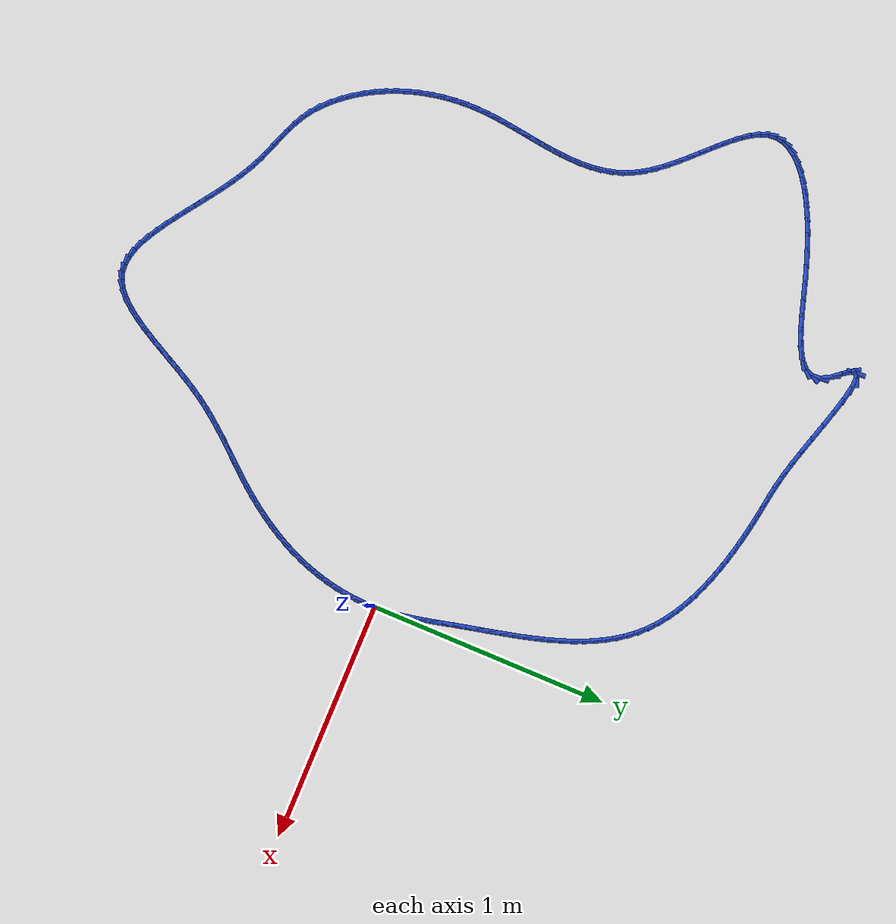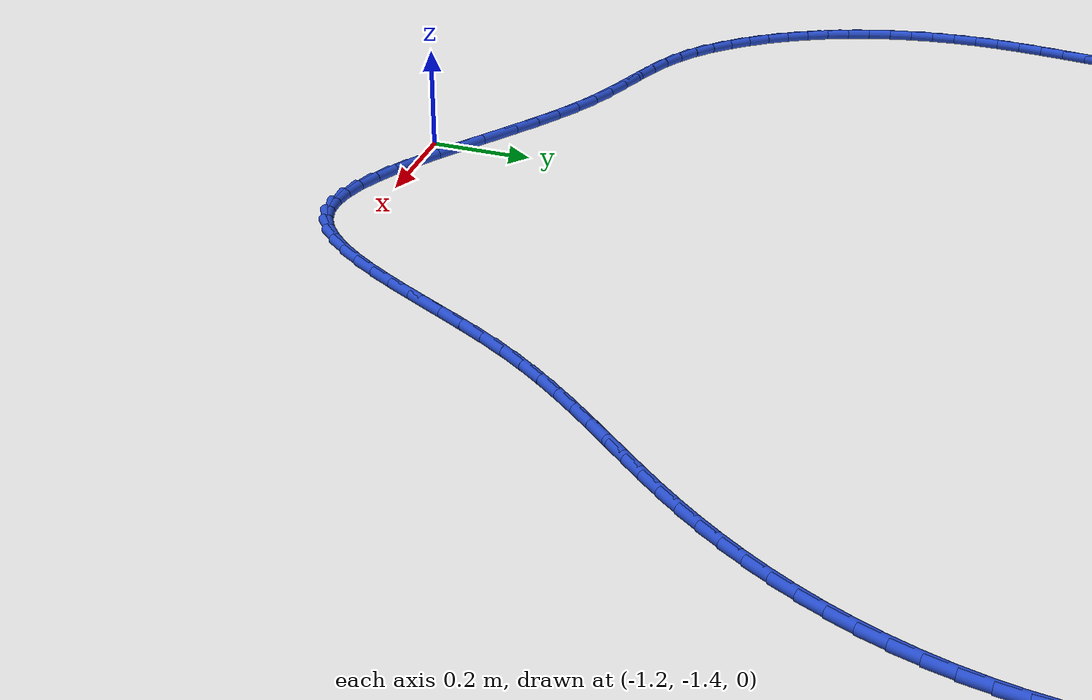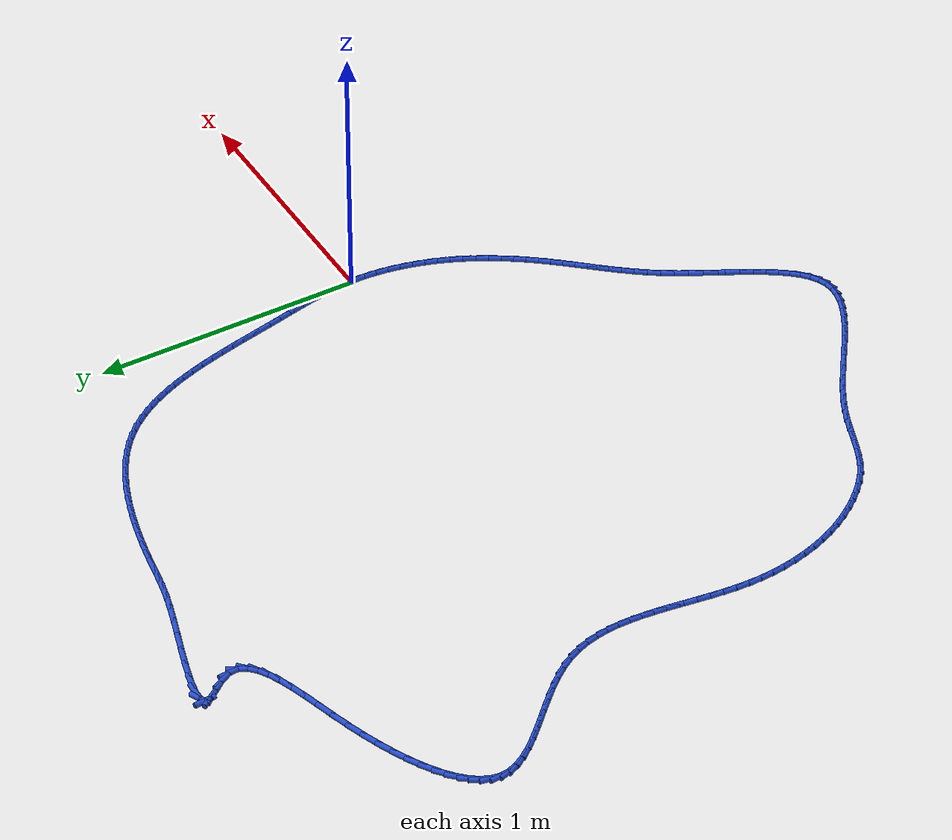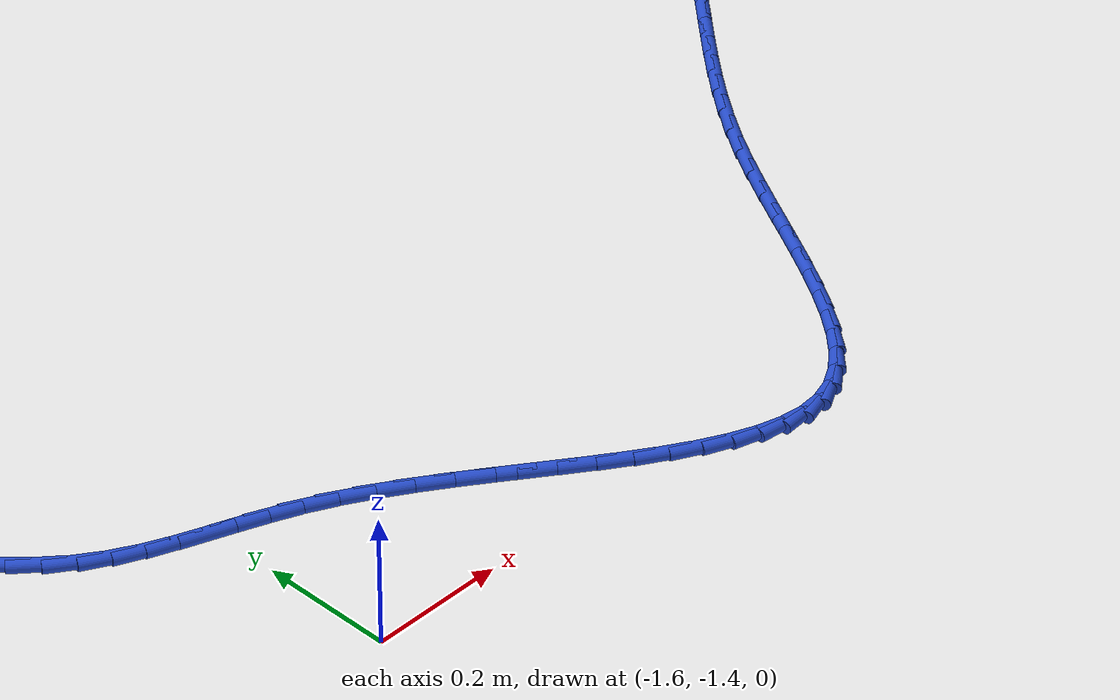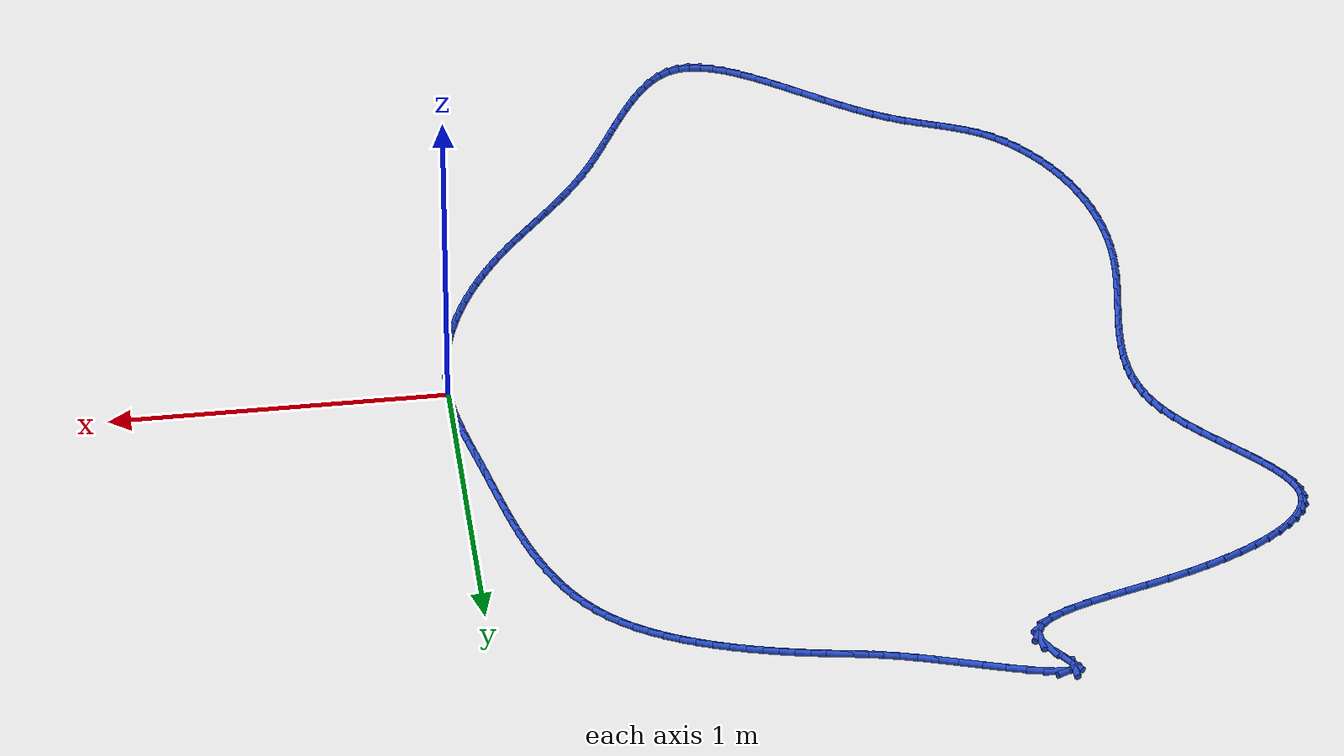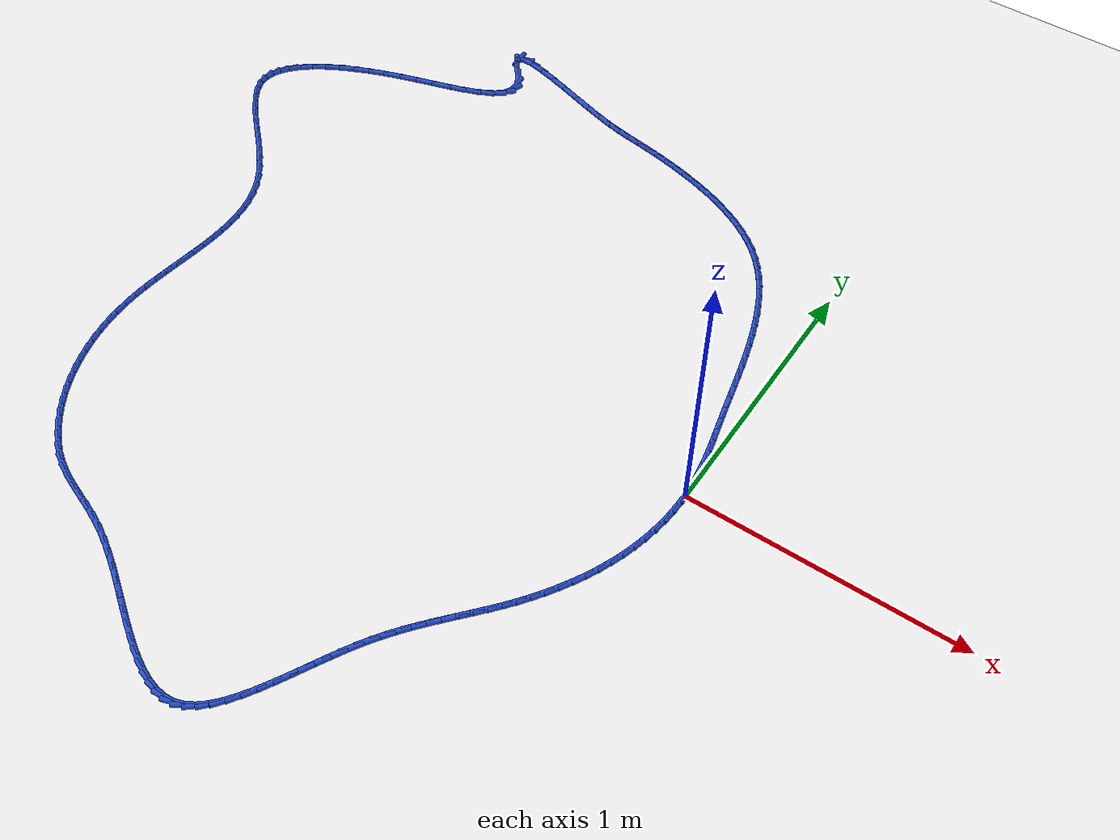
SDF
<sdf version="1.6">
 <world name="default">
  <light name="sun" type="directional">
   <pose>0 0 10 0 -0 0</pose>
   <diffuse>0.8 0.8 0.8 1</diffuse>
   <specular>0.2 0.2 0.2 1</specular>
   <attenuation>
    <range>1000</range>
    <constant>0.9</constant>
    <linear>0.01</linear>
    <quadratic>0.001</quadratic>
   </attenuation>
   <direction>-0.5 0.1 -0.9</direction>
  </light>
  <model name="ground_plane">
   <static>1</static>
   <link name="link">
    <collision name="collision">
     <geometry><plane><normal>0 0 1</normal><size>100 100</size></plane></geometry>
     <surface><friction><ode><mu>100</mu><mu2>50</mu2></ode></friction></surface>
    </collision>
    <visual name="visual">
     <cast_shadows>0</cast_shadows>
     <geometry><plane><normal>0 0 1</normal><size>100 100</size></plane></geometry>
     <material>
      <script><uri>file://media/materials/scripts/gazebo.material</uri><name>Gazebo/WhiteGlow</name></script>
     </material>
    </visual>
   </link>
  </model>
  <gravity>0 0 -9.8</gravity>
  <magnetic_field>6e-06 2.3e-05 -4.2e-05</magnetic_field>
  <atmosphere type="adiabatic"/>
  <physics name="default_physics" default="0" type="ode">
   <max_step_size>0.001</max_step_size>
   <real_time_factor>1</real_time_factor>
   <real_time_update_rate>1000</real_time_update_rate>
  </physics>
  <scene><ambient>0.4 0.4 0.4 1</ambient><background>0.7 0.7 0.7 1</background><shadows>1</shadows></scene>
  <spherical_coordinates>
   <surface_model>EARTH_WGS84</surface_model>
   <latitude_deg>0</latitude_deg>
   <longitude_deg>0</longitude_deg>
   <elevation>0</elevation>
   <heading_deg>0</heading_deg>
  </spherical_coordinates>
  <model name="line">
   <link name="link_0">
    <pose>-3.2959746043559335e-17 8.326672684688674e-17 0.01 0 1.57 -1.5091461247908138</pose>
    <collision name="collision">
     <geometry><cylinder><radius>0.01</radius><length>0.08</length></cylinder></geometry>
    </collision>
    <visual name="visual">
     <material>
      <script><name>Gazebo/Blue</name><uri>file://media/materials/scripts/gazebo.material</uri></script>
     </material>
     <geometry><cylinder><radius>0.01</radius><length>0.08</length></cylinder></geometry>
    </visual>
   </link>
   <link name="link_1">
    <pose>-0.002797153409749738 0.045313862125779925 0.01 0 1.57 -1.4577290639498848</pose>
    <collision name="collision">
     <geometry><cylinder><radius>0.01</radius><length>0.08</length></cylinder></geometry>
    </collision>
    <visual name="visual">
     <material>
      <script><name>Gazebo/Blue</name><uri>file://media/materials/scripts/gazebo.material</uri></script>
     </material>
     <geometry><cylinder><radius>0.01</radius><length>0.08</length></cylinder></geometry>
    </visual>
   </link>
   <link name="link_2">
    <pose>-0.007915810302056549 0.09039168126019784 0.01 0 1.57 -1.415455938503338</pose>
    <collision name="collision">
     <geometry><cylinder><radius>0.01</radius><length>0.08</length></cylinder></geometry>
    </collision>
    <visual name="visual">
     <material>
      <script><name>Gazebo/Blue</name><uri>file://media/materials/scripts/gazebo.material</uri></script>
     </material>
     <geometry><cylinder><radius>0.01</radius><length>0.08</length></cylinder></geometry>
    </visual>
   </link>
   <link name="link_3">
    <pose>-0.01495766580259047 0.13535823994639926 0.01 0 1.57 -1.3825938123735941</pose>
    <collision name="collision">
     <geometry><cylinder><radius>0.01</radius><length>0.08</length></cylinder></geometry>
    </collision>
    <visual name="visual">
     <material>
      <script><name>Gazebo/Blue</name><uri>file://media/materials/scripts/gazebo.material</uri></script>
     </material>
     <geometry><cylinder><radius>0.01</radius><length>0.08</length></cylinder></geometry>
    </visual>
   </link>
   <link name="link_4">
    <pose>-0.023524415037021518 0.1803383207275299 0.01 0 1.57 -1.3591708956164776</pose>
    <collision name="collision">
     <geometry><cylinder><radius>0.01</radius><length>0.08</length></cylinder></geometry>
    </collision>
    <visual name="visual">
     <material>
      <script><name>Gazebo/Blue</name><uri>file://media/materials/scripts/gazebo.material</uri></script>
     </material>
     <geometry><cylinder><radius>0.01</radius><length>0.08</length></cylinder></geometry>
    </visual>
   </link>
   <link name="link_5">
    <pose>-0.033217753131019635 0.22545670614673508 0.01 0 1.57 -1.3450652586535616</pose>
    <collision name="collision">
     <geometry><cylinder><radius>0.01</radius><length>0.08</length></cylinder></geometry>
    </collision>
    <visual name="visual">
     <material>
      <script><name>Gazebo/Blue</name><uri>file://media/materials/scripts/gazebo.material</uri></script>
     </material>
     <geometry><cylinder><radius>0.01</radius><length>0.08</length></cylinder></geometry>
    </visual>
   </link>
   <link name="link_6">
    <pose>-0.04363937521025485 0.27083817874716043 0.01 0 1.57 -1.3400712112427253</pose>
    <collision name="collision">
     <geometry><cylinder><radius>0.01</radius><length>0.08</length></cylinder></geometry>
    </collision>
    <visual name="visual">
     <material>
      <script><name>Gazebo/Blue</name><uri>file://media/materials/scripts/gazebo.material</uri></script>
     </material>
     <geometry><cylinder><radius>0.01</radius><length>0.08</length></cylinder></geometry>
    </visual>
   </link>
   <link name="link_7">
    <pose>-0.05439097640039716 0.31660752107195145 0.01 0 1.57 -1.3437348259160058</pose>
    <collision name="collision">
     <geometry><cylinder><radius>0.01</radius><length>0.08</length></cylinder></geometry>
    </collision>
    <visual name="visual">
     <material>
      <script><name>Gazebo/Blue</name><uri>file://media/materials/scripts/gazebo.material</uri></script>
     </material>
     <geometry><cylinder><radius>0.01</radius><length>0.08</length></cylinder></geometry>
    </visual>
   </link>
   <link name="link_8">
    <pose>-0.06508317171869205 0.3628848879630075 0.01 0 1.57 -1.349807010793291</pose>
    <collision name="collision">
     <geometry><cylinder><radius>0.01</radius><length>0.08</length></cylinder></geometry>
    </collision>
    <visual name="visual">
     <material>
      <script><name>Gazebo/Blue</name><uri>file://media/materials/scripts/gazebo.material</uri></script>
     </material>
     <geometry><cylinder><radius>0.01</radius><length>0.08</length></cylinder></geometry>
    </visual>
   </link>
   <link name="link_9">
    <pose>-0.07559017495311561 0.40965367740263386 0.01 0 1.57 -1.351460180213948</pose>
    <collision name="collision">
     <geometry><cylinder><radius>0.01</radius><length>0.08</length></cylinder></geometry>
    </collision>
    <visual name="visual">
     <material>
      <script><name>Gazebo/Blue</name><uri>file://media/materials/scripts/gazebo.material</uri></script>
     </material>
     <geometry><cylinder><radius>0.01</radius><length>0.08</length></cylinder></geometry>
    </visual>
   </link>
   <link name="link_10">
    <pose>-0.08608704371158694 0.45674120752523006 0.01 0 1.57 -1.3484228058666943</pose>
    <collision name="collision">
     <geometry><cylinder><radius>0.01</radius><length>0.08</length></cylinder></geometry>
    </collision>
    <visual name="visual">
     <material>
      <script><name>Gazebo/Blue</name><uri>file://media/materials/scripts/gazebo.material</uri></script>
     </material>
     <geometry><cylinder><radius>0.01</radius><length>0.08</length></cylinder></geometry>
    </visual>
   </link>
   <link name="link_11">
    <pose>-0.09676524531468637 0.5039662829931325 0.01 0 1.57 -1.3407202920912638</pose>
    <collision name="collision">
     <geometry><cylinder><radius>0.01</radius><length>0.08</length></cylinder></geometry>
    </collision>
    <visual name="visual">
     <material>
      <script><name>Gazebo/Blue</name><uri>file://media/materials/scripts/gazebo.material</uri></script>
     </material>
     <geometry><cylinder><radius>0.01</radius><length>0.08</length></cylinder></geometry>
    </visual>
   </link>
   <link name="link_12">
    <pose>-0.1078162470829944 0.5511477084686782 0.01 0 1.57 -1.32830211091923</pose>
    <collision name="collision">
     <geometry><cylinder><radius>0.01</radius><length>0.08</length></cylinder></geometry>
    </collision>
    <visual name="visual">
     <material>
      <script><name>Gazebo/Blue</name><uri>file://media/materials/scripts/gazebo.material</uri></script>
     </material>
     <geometry><cylinder><radius>0.01</radius><length>0.08</length></cylinder></geometry>
    </visual>
   </link>
   <link name="link_13">
    <pose>-0.1194315163370914 0.5981042886142037 0.01 0 1.57 -1.3110459625621749</pose>
    <collision name="collision">
     <geometry><cylinder><radius>0.01</radius><length>0.08</length></cylinder></geometry>
    </collision>
    <visual name="visual">
     <material>
      <script><name>Gazebo/Blue</name><uri>file://media/materials/scripts/gazebo.material</uri></script>
     </material>
     <geometry><cylinder><radius>0.01</radius><length>0.08</length></cylinder></geometry>
    </visual>
   </link>
   <link name="link_14">
    <pose>-0.13180252039755783 0.6446548280920457 0.01 0 1.57 -1.2887627219509084</pose>
    <collision name="collision">
     <geometry><cylinder><radius>0.01</radius><length>0.08</length></cylinder></geometry>
    </collision>
    <visual name="visual">
     <material>
      <script><name>Gazebo/Blue</name><uri>file://media/materials/scripts/gazebo.material</uri></script>
     </material>
     <geometry><cylinder><radius>0.01</radius><length>0.08</length></cylinder></geometry>
    </visual>
   </link>
   <link name="link_15">
    <pose>-0.14512072658497413 0.6906181315645412 0.01 0 1.57 -1.2612034450473564</pose>
    <collision name="collision">
     <geometry><cylinder><radius>0.01</radius><length>0.08</length></cylinder></geometry>
    </collision>
    <visual name="visual">
     <material>
      <script><name>Gazebo/Blue</name><uri>file://media/materials/scripts/gazebo.material</uri></script>
     </material>
     <geometry><cylinder><radius>0.01</radius><length>0.08</length></cylinder></geometry>
    </visual>
   </link>
   <link name="link_16">
    <pose>-0.1595776022199206 0.7358130036940264 0.01 0 1.57 -1.228070300148383</pose>
    <collision name="collision">
     <geometry><cylinder><radius>0.01</radius><length>0.08</length></cylinder></geometry>
    </collision>
    <visual name="visual">
     <material>
      <script><name>Gazebo/Blue</name><uri>file://media/materials/scripts/gazebo.material</uri></script>
     </material>
     <geometry><cylinder><radius>0.01</radius><length>0.08</length></cylinder></geometry>
    </visual>
   </link>
   <link name="link_17">
    <pose>-0.1753646146229778 0.7800582491428383 0.01 0 1.57 -1.1890339592401604</pose>
    <collision name="collision">
     <geometry><cylinder><radius>0.01</radius><length>0.08</length></cylinder></geometry>
    </collision>
    <visual name="visual">
     <material>
      <script><name>Gazebo/Blue</name><uri>file://media/materials/scripts/gazebo.material</uri></script>
     </material>
     <geometry><cylinder><radius>0.01</radius><length>0.08</length></cylinder></geometry>
    </visual>
   </link>
   <link name="link_18">
    <pose>-0.19267323111472606 0.8231726725733136 0.01 0 1.57 -1.143760611868172</pose>
    <collision name="collision">
     <geometry><cylinder><radius>0.01</radius><length>0.08</length></cylinder></geometry>
    </collision>
    <visual name="visual">
     <material>
      <script><name>Gazebo/Blue</name><uri>file://media/materials/scripts/gazebo.material</uri></script>
     </material>
     <geometry><cylinder><radius>0.01</radius><length>0.08</length></cylinder></geometry>
    </visual>
   </link>
   <link name="link_19">
    <pose>-0.21169491901574583 0.8649750786477887 0.01 0 1.57 -1.0919520369672038</pose>
    <collision name="collision">
     <geometry><cylinder><radius>0.01</radius><length>0.08</length></cylinder></geometry>
    </collision>
    <visual name="visual">
     <material>
      <script><name>Gazebo/Blue</name><uri>file://media/materials/scripts/gazebo.material</uri></script>
     </material>
     <geometry><cylinder><radius>0.01</radius><length>0.08</length></cylinder></geometry>
    </visual>
   </link>
   <link name="link_20">
    <pose>-0.23262114564661762 0.905284272028601 0.01 0 1.57 -1.0334014922247443</pose>
    <collision name="collision">
     <geometry><cylinder><radius>0.01</radius><length>0.08</length></cylinder></geometry>
    </collision>
    <visual name="visual">
     <material>
      <script><name>Gazebo/Blue</name><uri>file://media/materials/scripts/gazebo.material</uri></script>
     </material>
     <geometry><cylinder><radius>0.01</radius><length>0.08</length></cylinder></geometry>
    </visual>
   </link>
   <link name="link_21">
    <pose>-0.2556433783279218 0.9439190573780865 0.01 0 1.57 -0.9680656692108975</pose>
    <collision name="collision">
     <geometry><cylinder><radius>0.01</radius><length>0.08</length></cylinder></geometry>
    </collision>
    <visual name="visual">
     <material>
      <script><name>Gazebo/Blue</name><uri>file://media/materials/scripts/gazebo.material</uri></script>
     </material>
     <geometry><cylinder><radius>0.01</radius><length>0.08</length></cylinder></geometry>
    </visual>
   </link>
   <link name="link_22">
    <pose>-0.2809530843802387 0.9806982393585824 0.01 0 1.57 -0.8961477063270991</pose>
    <collision name="collision">
     <geometry><cylinder><radius>0.01</radius><length>0.08</length></cylinder></geometry>
    </collision>
    <visual name="visual">
     <material>
      <script><name>Gazebo/Blue</name><uri>file://media/materials/scripts/gazebo.material</uri></script>
     </material>
     <geometry><cylinder><radius>0.01</radius><length>0.08</length></cylinder></geometry>
    </visual>
   </link>
   <link name="link_23">
    <pose>-0.3087417311241488 1.0154406226324248 0.01 0 1.57 -0.8181781217192209</pose>
    <collision name="collision">
     <geometry><cylinder><radius>0.01</radius><length>0.08</length></cylinder></geometry>
    </collision>
    <visual name="visual">
     <material>
      <script><name>Gazebo/Blue</name><uri>file://media/materials/scripts/gazebo.material</uri></script>
     </material>
     <geometry><cylinder><radius>0.01</radius><length>0.08</length></cylinder></geometry>
    </visual>
   </link>
   <link name="link_24">
    <pose>-0.3392007858802324 1.0479650118619506 0.01 0 1.57 -0.735405458996308</pose>
    <collision name="collision">
     <geometry><cylinder><radius>0.01</radius><length>0.08</length></cylinder></geometry>
    </collision>
    <visual name="visual">
     <material>
      <script><name>Gazebo/Blue</name><uri>file://media/materials/scripts/gazebo.material</uri></script>
     </material>
     <geometry><cylinder><radius>0.01</radius><length>0.08</length></cylinder></geometry>
    </visual>
   </link>
   <link name="link_25">
    <pose>-0.37250794785718017 1.0780979850864663 0.01 0 1.57 -0.6552173305871156</pose>
    <collision name="collision">
     <geometry><cylinder><radius>0.01</radius><length>0.08</length></cylinder></geometry>
    </collision>
    <visual name="visual">
     <material>
      <script><name>Gazebo/Blue</name><uri>file://media/materials/scripts/gazebo.material</uri></script>
     </material>
     <geometry><cylinder><radius>0.01</radius><length>0.08</length></cylinder></geometry>
    </visual>
   </link>
   <link name="link_26">
    <pose>-0.4085763739388094 1.1058154790396242 0.01 0 1.57 -0.5833674977482303</pose>
    <collision name="collision">
     <geometry><cylinder><radius>0.01</radius><length>0.08</length></cylinder></geometry>
    </collision>
    <visual name="visual">
     <material>
      <script><name>Gazebo/Blue</name><uri>file://media/materials/scripts/gazebo.material</uri></script>
     </material>
     <geometry><cylinder><radius>0.01</radius><length>0.08</length></cylinder></geometry>
    </visual>
   </link>
   <link name="link_27">
    <pose>-0.4470807555240978 1.1312280663530563 0.01 0 1.57 -0.5195054837755422</pose>
    <collision name="collision">
     <geometry><cylinder><radius>0.01</radius><length>0.08</length></cylinder></geometry>
    </collision>
    <visual name="visual">
     <material>
      <script><name>Gazebo/Blue</name><uri>file://media/materials/scripts/gazebo.material</uri></script>
     </material>
     <geometry><cylinder><radius>0.01</radius><length>0.08</length></cylinder></geometry>
    </visual>
   </link>
   <link name="link_28">
    <pose>-0.4876872488817966 1.1544511385315457 0.01 0 1.57 -0.4629217789890496</pose>
    <collision name="collision">
     <geometry><cylinder><radius>0.01</radius><length>0.08</length></cylinder></geometry>
    </collision>
    <visual name="visual">
     <material>
      <script><name>Gazebo/Blue</name><uri>file://media/materials/scripts/gazebo.material</uri></script>
     </material>
     <geometry><cylinder><radius>0.01</radius><length>0.08</length></cylinder></geometry>
    </visual>
   </link>
   <link name="link_29">
    <pose>-0.5300620102806565 1.1756000870798755 0.01 0 1.57 -0.41286437736375453</pose>
    <collision name="collision">
     <geometry><cylinder><radius>0.01</radius><length>0.08</length></cylinder></geometry>
    </collision>
    <visual name="visual">
     <material>
      <script><name>Gazebo/Blue</name><uri>file://media/materials/scripts/gazebo.material</uri></script>
     </material>
     <geometry><cylinder><radius>0.01</radius><length>0.08</length></cylinder></geometry>
    </visual>
   </link>
   <link name="link_30">
    <pose>-0.5738711959894282 1.1947903035028289 0.01 0 1.57 -0.36860629536668515</pose>
    <collision name="collision">
     <geometry><cylinder><radius>0.01</radius><length>0.08</length></cylinder></geometry>
    </collision>
    <visual name="visual">
     <material>
      <script><name>Gazebo/Blue</name><uri>file://media/materials/scripts/gazebo.material</uri></script>
     </material>
     <geometry><cylinder><radius>0.01</radius><length>0.08</length></cylinder></geometry>
    </visual>
   </link>
   <link name="link_31">
    <pose>-0.6187809622768625 1.2121371793051892 0.01 0 1.57 -0.3294823951898498</pose>
    <collision name="collision">
     <geometry><cylinder><radius>0.01</radius><length>0.08</length></cylinder></geometry>
    </collision>
    <visual name="visual">
     <material>
      <script><name>Gazebo/Blue</name><uri>file://media/materials/scripts/gazebo.material</uri></script>
     </material>
     <geometry><cylinder><radius>0.01</radius><length>0.08</length></cylinder></geometry>
    </visual>
   </link>
   <link name="link_32">
    <pose>-0.6644574654117111 1.2277561059917397 0.01 0 1.57 -0.29490630756532477</pose>
    <collision name="collision">
     <geometry><cylinder><radius>0.01</radius><length>0.08</length></cylinder></geometry>
    </collision>
    <visual name="visual">
     <material>
      <script><name>Gazebo/Blue</name><uri>file://media/materials/scripts/gazebo.material</uri></script>
     </material>
     <geometry><cylinder><radius>0.01</radius><length>0.08</length></cylinder></geometry>
    </visual>
   </link>
   <link name="link_33">
    <pose>-0.7105668616627239 1.241762475067263 0.01 0 1.57 -0.26437578575754683</pose>
    <collision name="collision">
     <geometry><cylinder><radius>0.01</radius><length>0.08</length></cylinder></geometry>
    </collision>
    <visual name="visual">
     <material>
      <script><name>Gazebo/Blue</name><uri>file://media/materials/scripts/gazebo.material</uri></script>
     </material>
     <geometry><cylinder><radius>0.01</radius><length>0.08</length></cylinder></geometry>
    </visual>
   </link>
   <link name="link_34">
    <pose>-0.7567753072986521 1.254271678036543 0.01 0 1.57 -0.23747227886781153</pose>
    <collision name="collision">
     <geometry><cylinder><radius>0.01</radius><length>0.08</length></cylinder></geometry>
    </collision>
    <visual name="visual">
     <material>
      <script><name>Gazebo/Blue</name><uri>file://media/materials/scripts/gazebo.material</uri></script>
     </material>
     <geometry><cylinder><radius>0.01</radius><length>0.08</length></cylinder></geometry>
    </visual>
   </link>
   <link name="link_35">
    <pose>-0.8027489585882469 1.2653991064043624 0.01 0 1.57 -0.2138585798041829</pose>
    <collision name="collision">
     <geometry><cylinder><radius>0.01</radius><length>0.08</length></cylinder></geometry>
    </collision>
    <visual name="visual">
     <material>
      <script><name>Gazebo/Blue</name><uri>file://media/materials/scripts/gazebo.material</uri></script>
     </material>
     <geometry><cylinder><radius>0.01</radius><length>0.08</length></cylinder></geometry>
    </visual>
   </link>
   <link name="link_36">
    <pose>-0.8481539718002589 1.2752601516755047 0.01 0 1.57 -0.19327720304860432</pose>
    <collision name="collision">
     <geometry><cylinder><radius>0.01</radius><length>0.08</length></cylinder></geometry>
    </collision>
    <visual name="visual">
     <material>
      <script><name>Gazebo/Blue</name><uri>file://media/materials/scripts/gazebo.material</uri></script>
     </material>
     <geometry><cylinder><radius>0.01</radius><length>0.08</length></cylinder></geometry>
    </visual>
   </link>
   <link name="link_37">
    <pose>-0.8926565032034385 1.2839702053547524 0.01 0 1.57 -0.1755516325422416</pose>
    <collision name="collision">
     <geometry><cylinder><radius>0.01</radius><length>0.08</length></cylinder></geometry>
    </collision>
    <visual name="visual">
     <material>
      <script><name>Gazebo/Blue</name><uri>file://media/materials/scripts/gazebo.material</uri></script>
     </material>
     <geometry><cylinder><radius>0.01</radius><length>0.08</length></cylinder></geometry>
    </visual>
   </link>
   <link name="link_38">
    <pose>-0.9359227090665372 1.2916446589468895 0.01 0 1.57 -0.16073707792983374</pose>
    <collision name="collision">
     <geometry><cylinder><radius>0.01</radius><length>0.08</length></cylinder></geometry>
    </collision>
    <visual name="visual">
     <material>
      <script><name>Gazebo/Blue</name><uri>file://media/materials/scripts/gazebo.material</uri></script>
     </material>
     <geometry><cylinder><radius>0.01</radius><length>0.08</length></cylinder></geometry>
    </visual>
   </link>
   <link name="link_39">
    <pose>-0.9776432051211034 1.2984090459830482 0.01 0 1.57 -0.15516687904009258</pose>
    <collision name="collision">
     <geometry><cylinder><radius>0.01</radius><length>0.08</length></cylinder></geometry>
    </collision>
    <visual name="visual">
     <material>
      <script><name>Gazebo/Blue</name><uri>file://media/materials/scripts/gazebo.material</uri></script>
     </material>
     <geometry><cylinder><radius>0.01</radius><length>0.08</length></cylinder></geometry>
    </visual>
   </link>
   <link name="link_40">
    <pose>-1.0185002475422786 1.3048000800595643 0.01 0 1.57 -0.1674767321174801</pose>
    <collision name="collision">
     <geometry><cylinder><radius>0.01</radius><length>0.08</length></cylinder></geometry>
    </collision>
    <visual name="visual">
     <material>
      <script><name>Gazebo/Blue</name><uri>file://media/materials/scripts/gazebo.material</uri></script>
     </material>
     <geometry><cylinder><radius>0.01</radius><length>0.08</length></cylinder></geometry>
    </visual>
   </link>
   <link name="link_41">
    <pose>-1.0604883690901856 1.3118986054355204 0.01 0 1.57 -0.1949155802885259</pose>
    <collision name="collision">
     <geometry><cylinder><radius>0.01</radius><length>0.08</length></cylinder></geometry>
    </collision>
    <visual name="visual">
     <material>
      <script><name>Gazebo/Blue</name><uri>file://media/materials/scripts/gazebo.material</uri></script>
     </material>
     <geometry><cylinder><radius>0.01</radius><length>0.08</length></cylinder></geometry>
    </visual>
   </link>
   <link name="link_42">
    <pose>-1.1056922711747488 1.320822854469228 0.01 0 1.57 -0.23080585838114384</pose>
    <collision name="collision">
     <geometry><cylinder><radius>0.01</radius><length>0.08</length></cylinder></geometry>
    </collision>
    <visual name="visual">
     <material>
      <script><name>Gazebo/Blue</name><uri>file://media/materials/scripts/gazebo.material</uri></script>
     </material>
     <geometry><cylinder><radius>0.01</radius><length>0.08</length></cylinder></geometry>
    </visual>
   </link>
   <link name="link_43">
    <pose>-1.156196655205893 1.3326910595189985 0.01 0 1.57 -0.2674565600984572</pose>
    <collision name="collision">
     <geometry><cylinder><radius>0.01</radius><length>0.08</length></cylinder></geometry>
    </collision>
    <visual name="visual">
     <material>
      <script><name>Gazebo/Blue</name><uri>file://media/materials/scripts/gazebo.material</uri></script>
     </material>
     <geometry><cylinder><radius>0.01</radius><length>0.08</length></cylinder></geometry>
    </visual>
   </link>
   <link name="link_44">
    <pose>-1.2138484750460428 1.348488915038708 0.01 0 1.57 -0.2908408814250058</pose>
    <collision name="collision">
     <geometry><cylinder><radius>0.01</radius><length>0.08</length></cylinder></geometry>
    </collision>
    <visual name="visual">
     <material>
      <script><name>Gazebo/Blue</name><uri>file://media/materials/scripts/gazebo.material</uri></script>
     </material>
     <geometry><cylinder><radius>0.01</radius><length>0.08</length></cylinder></geometry>
    </visual>
   </link>
   <link name="link_45">
    <pose>-1.2775348231260304 1.3675520718300984 0.01 0 1.57 -0.2992209934138235</pose>
    <collision name="collision">
     <geometry><cylinder><radius>0.01</radius><length>0.08</length></cylinder></geometry>
    </collision>
    <visual name="visual">
     <material>
      <script><name>Gazebo/Blue</name><uri>file://media/materials/scripts/gazebo.material</uri></script>
     </material>
     <geometry><cylinder><radius>0.01</radius><length>0.08</length></cylinder></geometry>
    </visual>
   </link>
   <link name="link_46">
    <pose>-1.3441357934737994 1.3880973327180508 0.01 0 1.57 -0.295815088353115</pose>
    <collision name="collision">
     <geometry><cylinder><radius>0.01</radius><length>0.08</length></cylinder></geometry>
    </collision>
    <visual name="visual">
     <material>
      <script><name>Gazebo/Blue</name><uri>file://media/materials/scripts/gazebo.material</uri></script>
     </material>
     <geometry><cylinder><radius>0.01</radius><length>0.08</length></cylinder></geometry>
    </visual>
   </link>
   <link name="link_47">
    <pose>-1.4104933682964722 1.4083202542057947 0.01 0 1.57 -0.27989468889823294</pose>
    <collision name="collision">
     <geometry><cylinder><radius>0.01</radius><length>0.08</length></cylinder></geometry>
    </collision>
    <visual name="visual">
     <material>
      <script><name>Gazebo/Blue</name><uri>file://media/materials/scripts/gazebo.material</uri></script>
     </material>
     <geometry><cylinder><radius>0.01</radius><length>0.08</length></cylinder></geometry>
    </visual>
   </link>
   <link name="link_48">
    <pose>-1.473449529801171 1.4264163927965596 0.01 0 1.57 -0.24607528993753755</pose>
    <collision name="collision">
     <geometry><cylinder><radius>0.01</radius><length>0.08</length></cylinder></geometry>
    </collision>
    <visual name="visual">
     <material>
      <script><name>Gazebo/Blue</name><uri>file://media/materials/scripts/gazebo.material</uri></script>
     </material>
     <geometry><cylinder><radius>0.01</radius><length>0.08</length></cylinder></geometry>
    </visual>
   </link>
   <link name="link_49">
    <pose>-1.5298462601950193 1.440581304993576 0.01 0 1.57 -0.17865255584281298</pose>
    <collision name="collision">
     <geometry><cylinder><radius>0.01</radius><length>0.08</length></cylinder></geometry>
    </collision>
    <visual name="visual">
     <material>
      <script><name>Gazebo/Blue</name><uri>file://media/materials/scripts/gazebo.material</uri></script>
     </material>
     <geometry><cylinder><radius>0.01</radius><length>0.08</length></cylinder></geometry>
    </visual>
   </link>
   <link name="link_50">
    <pose>-1.576525541685138 1.449010547300073 0.01 0 1.57 -0.026296557602241002</pose>
    <collision name="collision">
     <geometry><cylinder><radius>0.01</radius><length>0.08</length></cylinder></geometry>
    </collision>
    <visual name="visual">
     <material>
      <script><name>Gazebo/Blue</name><uri>file://media/materials/scripts/gazebo.material</uri></script>
     </material>
     <geometry><cylinder><radius>0.01</radius><length>0.08</length></cylinder></geometry>
    </visual>
   </link>
   <link name="link_51">
    <pose>-1.6103293564786512 1.4498996762192808 0.01 0 1.57 0.4441148483691678</pose>
    <collision name="collision">
     <geometry><cylinder><radius>0.01</radius><length>0.08</length></cylinder></geometry>
    </collision>
    <visual name="visual">
     <material>
      <script><name>Gazebo/Blue</name><uri>file://media/materials/scripts/gazebo.material</uri></script>
     </material>
     <geometry><cylinder><radius>0.01</radius><length>0.08</length></cylinder></geometry>
    </visual>
   </link>
   <link name="link_52">
    <pose>-1.6280996867826814 1.4414442482544296 0.01 0 1.57 -1.4984305182070288</pose>
    <collision name="collision">
     <geometry><cylinder><radius>0.01</radius><length>0.08</length></cylinder></geometry>
    </collision>
    <visual name="visual">
     <material>
      <script><name>Gazebo/Blue</name><uri>file://media/materials/scripts/gazebo.material</uri></script>
     </material>
     <geometry><cylinder><radius>0.01</radius><length>0.08</length></cylinder></geometry>
    </visual>
   </link>
   <link name="link_53">
    <pose>-1.6266785148043492 1.421839819908748 0.01 0 1.57 -0.9635703298265265</pose>
    <collision name="collision">
     <geometry><cylinder><radius>0.01</radius><length>0.08</length></cylinder></geometry>
    </collision>
    <visual name="visual">
     <material>
      <script><name>Gazebo/Blue</name><uri>file://media/materials/scripts/gazebo.material</uri></script>
     </material>
     <geometry><cylinder><radius>0.01</radius><length>0.08</length></cylinder></geometry>
    </visual>
   </link>
   <link name="link_54">
    <pose>-1.604581130145524 1.3900357676664892 0.01 0 1.57 -0.9042869947587944</pose>
    <collision name="collision">
     <geometry><cylinder><radius>0.01</radius><length>0.08</length></cylinder></geometry>
    </collision>
    <visual name="visual">
     <material>
      <script><name>Gazebo/Blue</name><uri>file://media/materials/scripts/gazebo.material</uri></script>
     </material>
     <geometry><cylinder><radius>0.01</radius><length>0.08</length></cylinder></geometry>
    </visual>
   </link>
   <link name="link_55">
    <pose>-1.5739822433209991 1.3511349963150063 0.01 0 1.57 -1.072262286283603</pose>
    <collision name="collision">
     <geometry><cylinder><radius>0.01</radius><length>0.08</length></cylinder></geometry>
    </collision>
    <visual name="visual">
     <material>
      <script><name>Gazebo/Blue</name><uri>file://media/materials/scripts/gazebo.material</uri></script>
     </material>
     <geometry><cylinder><radius>0.01</radius><length>0.08</length></cylinder></geometry>
    </visual>
   </link>
   <link name="link_56">
    <pose>-1.5532462784882939 1.313045458852693 0.01 0 1.57 -1.48903114766833</pose>
    <collision name="collision">
     <geometry><cylinder><radius>0.01</radius><length>0.08</length></cylinder></geometry>
    </collision>
    <visual name="visual">
     <material>
      <script><name>Gazebo/Blue</name><uri>file://media/materials/scripts/gazebo.material</uri></script>
     </material>
     <geometry><cylinder><radius>0.01</radius><length>0.08</length></cylinder></geometry>
    </visual>
   </link>
   <link name="link_57">
    <pose>-1.5504904577430834 1.2794165149895513 0.01 0 1.57 1.145692306508358</pose>
    <collision name="collision">
     <geometry><cylinder><radius>0.01</radius><length>0.08</length></cylinder></geometry>
    </collision>
    <visual name="visual">
     <material>
      <script><name>Gazebo/Blue</name><uri>file://media/materials/scripts/gazebo.material</uri></script>
     </material>
     <geometry><cylinder><radius>0.01</radius><length>0.08</length></cylinder></geometry>
    </visual>
   </link>
   <link name="link_58">
    <pose>-1.563910443191096 1.2497727466809039 0.01 0 1.57 0.7651682351749294</pose>
    <collision name="collision">
     <geometry><cylinder><radius>0.01</radius><length>0.08</length></cylinder></geometry>
    </collision>
    <visual name="visual">
     <material>
      <script><name>Gazebo/Blue</name><uri>file://media/materials/scripts/gazebo.material</uri></script>
     </material>
     <geometry><cylinder><radius>0.01</radius><length>0.08</length></cylinder></geometry>
    </visual>
   </link>
   <link name="link_59">
    <pose>-1.5912984645674375 1.2234710133798115 0.01 0 1.57 0.5425554309416638</pose>
    <collision name="collision">
     <geometry><cylinder><radius>0.01</radius><length>0.08</length></cylinder></geometry>
    </collision>
    <visual name="visual">
     <material>
      <script><name>Gazebo/Blue</name><uri>file://media/materials/scripts/gazebo.material</uri></script>
     </material>
     <geometry><cylinder><radius>0.01</radius><length>0.08</length></cylinder></geometry>
    </visual>
   </link>
   <link name="link_60">
    <pose>-1.6304467516072156 1.199868174539333 0.01 0 1.57 0.41654773790873073</pose>
    <collision name="collision">
     <geometry><cylinder><radius>0.01</radius><length>0.08</length></cylinder></geometry>
    </collision>
    <visual name="visual">
     <material>
      <script><name>Gazebo/Blue</name><uri>file://media/materials/scripts/gazebo.material</uri></script>
     </material>
     <geometry><cylinder><radius>0.01</radius><length>0.08</length></cylinder></geometry>
    </visual>
   </link>
   <link name="link_61">
    <pose>-1.6791475340455353 1.1783210896125293 0.01 0 1.57 0.34489341332329615</pose>
    <collision name="collision">
     <geometry><cylinder><radius>0.01</radius><length>0.08</length></cylinder></geometry>
    </collision>
    <visual name="visual">
     <material>
      <script><name>Gazebo/Blue</name><uri>file://media/materials/scripts/gazebo.material</uri></script>
     </material>
     <geometry><cylinder><radius>0.01</radius><length>0.08</length></cylinder></geometry>
    </visual>
   </link>
   <link name="link_62">
    <pose>-1.7351930416175045 1.1581866180524611 0.01 0 1.57 0.30653596822226276</pose>
    <collision name="collision">
     <geometry><cylinder><radius>0.01</radius><length>0.08</length></cylinder></geometry>
    </collision>
    <visual name="visual">
     <material>
      <script><name>Gazebo/Blue</name><uri>file://media/materials/scripts/gazebo.material</uri></script>
     </material>
     <geometry><cylinder><radius>0.01</radius><length>0.08</length></cylinder></geometry>
    </visual>
   </link>
   <link name="link_63">
    <pose>-1.7963755040582297 1.1388216193121876 0.01 0 1.57 0.2915308086980983</pose>
    <collision name="collision">
     <geometry><cylinder><radius>0.01</radius><length>0.08</length></cylinder></geometry>
    </collision>
    <visual name="visual">
     <material>
      <script><name>Gazebo/Blue</name><uri>file://media/materials/scripts/gazebo.material</uri></script>
     </material>
     <geometry><cylinder><radius>0.01</radius><length>0.08</length></cylinder></geometry>
    </visual>
   </link>
   <link name="link_64">
    <pose>-1.8604871511028163 1.1195829528447694 0.01 0 1.57 0.2957749927005786</pose>
    <collision name="collision">
     <geometry><cylinder><radius>0.01</radius><length>0.08</length></cylinder></geometry>
    </collision>
    <visual name="visual">
     <material>
      <script><name>Gazebo/Blue</name><uri>file://media/materials/scripts/gazebo.material</uri></script>
     </material>
     <geometry><cylinder><radius>0.01</radius><length>0.08</length></cylinder></geometry>
    </visual>
   </link>
   <link name="link_65">
    <pose>-1.9253202124863715 1.0998274781032662 0.01 0 1.57 0.31795910009557055</pose>
    <collision name="collision">
     <geometry><cylinder><radius>0.01</radius><length>0.08</length></cylinder></geometry>
    </collision>
    <visual name="visual">
     <material>
      <script><name>Gazebo/Blue</name><uri>file://media/materials/scripts/gazebo.material</uri></script>
     </material>
     <geometry><cylinder><radius>0.01</radius><length>0.08</length></cylinder></geometry>
    </visual>
   </link>
   <link name="link_66">
    <pose>-1.9887548408993452 1.0789494987074935 0.01 0 1.57 0.34953979547859126</pose>
    <collision name="collision">
     <geometry><cylinder><radius>0.01</radius><length>0.08</length></cylinder></geometry>
    </collision>
    <visual name="visual">
     <material>
      <script><name>Gazebo/Blue</name><uri>file://media/materials/scripts/gazebo.material</uri></script>
     </material>
     <geometry><cylinder><radius>0.01</radius><length>0.08</length></cylinder></geometry>
    </visual>
   </link>
   <link name="link_67">
    <pose>-2.0496406555161633 1.0567561895751814 0.01 0 1.57 0.3854222471180839</pose>
    <collision name="collision">
     <geometry><cylinder><radius>0.01</radius><length>0.08</length></cylinder></geometry>
    </collision>
    <visual name="visual">
     <material>
      <script><name>Gazebo/Blue</name><uri>file://media/materials/scripts/gazebo.material</uri></script>
     </material>
     <geometry><cylinder><radius>0.01</radius><length>0.08</length></cylinder></geometry>
    </visual>
   </link>
   <link name="link_68">
    <pose>-2.107428617821896 1.0333108221311513 0.01 0 1.57 0.4268824343481213</pose>
    <collision name="collision">
     <geometry><cylinder><radius>0.01</radius><length>0.08</length></cylinder></geometry>
    </collision>
    <visual name="visual">
     <material>
      <script><name>Gazebo/Blue</name><uri>file://media/materials/scripts/gazebo.material</uri></script>
     </material>
     <geometry><cylinder><radius>0.01</radius><length>0.08</length></cylinder></geometry>
    </visual>
   </link>
   <link name="link_69">
    <pose>-2.1615786816910343 1.008680497431833 0.01 0 1.57 0.4757737800479558</pose>
    <collision name="collision">
     <geometry><cylinder><radius>0.01</radius><length>0.08</length></cylinder></geometry>
    </collision>
    <visual name="visual">
     <material>
      <script><name>Gazebo/Blue</name><uri>file://media/materials/scripts/gazebo.material</uri></script>
     </material>
     <geometry><cylinder><radius>0.01</radius><length>0.08</length></cylinder></geometry>
    </visual>
   </link>
   <link name="link_70">
    <pose>-2.2115508009980682 0.9829323165336572 0.01 0 1.57 0.5346553212865571</pose>
    <collision name="collision">
     <geometry><cylinder><radius>0.01</radius><length>0.08</length></cylinder></geometry>
    </collision>
    <visual name="visual">
     <material>
      <script><name>Gazebo/Blue</name><uri>file://media/materials/scripts/gazebo.material</uri></script>
     </material>
     <geometry><cylinder><radius>0.01</radius><length>0.08</length></cylinder></geometry>
    </visual>
   </link>
   <link name="link_71">
    <pose>-2.2568049296174864 0.9561333804930527 0.01 0 1.57 0.6071146066742659</pose>
    <collision name="collision">
     <geometry><cylinder><radius>0.01</radius><length>0.08</length></cylinder></geometry>
    </collision>
    <visual name="visual">
     <material>
      <script><name>Gazebo/Blue</name><uri>file://media/materials/scripts/gazebo.material</uri></script>
     </material>
     <geometry><cylinder><radius>0.01</radius><length>0.08</length></cylinder></geometry>
    </visual>
   </link>
   <link name="link_72">
    <pose>-2.2968010214237786 0.9283507903664507 0.01 0 1.57 0.6981935841607546</pose>
    <collision name="collision">
     <geometry><cylinder><radius>0.01</radius><length>0.08</length></cylinder></geometry>
    </collision>
    <visual name="visual">
     <material>
      <script><name>Gazebo/Blue</name><uri>file://media/materials/scripts/gazebo.material</uri></script>
     </material>
     <geometry><cylinder><radius>0.01</radius><length>0.08</length></cylinder></geometry>
    </visual>
   </link>
   <link name="link_73">
    <pose>-2.330999030291435 0.8996516472102802 0.01 0 1.57 0.8148054678981683</pose>
    <collision name="collision">
     <geometry><cylinder><radius>0.01</radius><length>0.08</length></cylinder></geometry>
    </collision>
    <visual name="visual">
     <material>
      <script><name>Gazebo/Blue</name><uri>file://media/materials/scripts/gazebo.material</uri></script>
     </material>
     <geometry><cylinder><radius>0.01</radius><length>0.08</length></cylinder></geometry>
    </visual>
   </link>
   <link name="link_74">
    <pose>-2.3588589100949453 0.8701030520809712 0.01 0 1.57 0.9656226809552602</pose>
    <collision name="collision">
     <geometry><cylinder><radius>0.01</radius><length>0.08</length></cylinder></geometry>
    </collision>
    <visual name="visual">
     <material>
      <script><name>Gazebo/Blue</name><uri>file://media/materials/scripts/gazebo.material</uri></script>
     </material>
     <geometry><cylinder><radius>0.01</radius><length>0.08</length></cylinder></geometry>
    </visual>
   </link>
   <link name="link_75">
    <pose>-2.3798406147087996 0.8397721060349541 0.01 0 1.57 1.1589058228469624</pose>
    <collision name="collision">
     <geometry><cylinder><radius>0.01</radius><length>0.08</length></cylinder></geometry>
    </collision>
    <visual name="visual">
     <material>
      <script><name>Gazebo/Blue</name><uri>file://media/materials/scripts/gazebo.material</uri></script>
     </material>
     <geometry><cylinder><radius>0.01</radius><length>0.08</length></cylinder></geometry>
    </visual>
   </link>
   <link name="link_76">
    <pose>-2.3934040980074864 0.8087259101286587 0.01 0 1.57 1.3957540265869801</pose>
    <collision name="collision">
     <geometry><cylinder><radius>0.01</radius><length>0.08</length></cylinder></geometry>
    </collision>
    <visual name="visual">
     <material>
      <script><name>Gazebo/Blue</name><uri>file://media/materials/scripts/gazebo.material</uri></script>
     </material>
     <geometry><cylinder><radius>0.01</radius><length>0.08</length></cylinder></geometry>
    </visual>
   </link>
   <link name="link_77">
    <pose>-2.399009313865496 0.7770315654185143 0.01 0 1.57 -1.482196314395727</pose>
    <collision name="collision">
     <geometry><cylinder><radius>0.01</radius><length>0.08</length></cylinder></geometry>
    </collision>
    <visual name="visual">
     <material>
      <script><name>Gazebo/Blue</name><uri>file://media/materials/scripts/gazebo.material</uri></script>
     </material>
     <geometry><cylinder><radius>0.01</radius><length>0.08</length></cylinder></geometry>
    </visual>
   </link>
   <link name="link_78">
    <pose>-2.3961420771294093 0.744754704922399 0.01 0 1.57 -1.2450248330038676</pose>
    <collision name="collision">
     <geometry><cylinder><radius>0.01</radius><length>0.08</length></cylinder></geometry>
    </collision>
    <visual name="visual">
     <material>
      <script><name>Gazebo/Blue</name><uri>file://media/materials/scripts/gazebo.material</uri></script>
     </material>
     <geometry><cylinder><radius>0.01</radius><length>0.08</length></cylinder></geometry>
    </visual>
   </link>
   <link name="link_79">
    <pose>-2.3850495198663983 0.7119177442947239 0.01 0 1.57 -1.0720881414288603</pose>
    <collision name="collision">
     <geometry><cylinder><radius>0.01</radius><length>0.08</length></cylinder></geometry>
    </collision>
    <visual name="visual">
     <material>
      <script><name>Gazebo/Blue</name><uri>file://media/materials/scripts/gazebo.material</uri></script>
     </material>
     <geometry><cylinder><radius>0.01</radius><length>0.08</length></cylinder></geometry>
    </visual>
   </link>
   <link name="link_80">
    <pose>-2.3668459981426637 0.6784938698624128 0.01 0 1.57 -0.9536956344488489</pose>
    <collision name="collision">
     <geometry><cylinder><radius>0.01</radius><length>0.08</length></cylinder></geometry>
    </collision>
    <visual name="visual">
     <material>
      <script><name>Gazebo/Blue</name><uri>file://media/materials/scripts/gazebo.material</uri></script>
     </material>
     <geometry><cylinder><radius>0.01</radius><length>0.08</length></cylinder></geometry>
    </visual>
   </link>
   <link name="link_81">
    <pose>-2.342693023057389 0.6444535911231485 0.01 0 1.57 -0.8754497083096799</pose>
    <collision name="collision">
     <geometry><cylinder><radius>0.01</radius><length>0.08</length></cylinder></geometry>
    </collision>
    <visual name="visual">
     <material>
      <script><name>Gazebo/Blue</name><uri>file://media/materials/scripts/gazebo.material</uri></script>
     </material>
     <geometry><cylinder><radius>0.01</radius><length>0.08</length></cylinder></geometry>
    </visual>
   </link>
   <link name="link_82">
    <pose>-2.3137521057097565 0.6097674175746115 0.01 0 1.57 -0.8265093204830671</pose>
    <collision name="collision">
     <geometry><cylinder><radius>0.01</radius><length>0.08</length></cylinder></geometry>
    </collision>
    <visual name="visual">
     <material>
      <script><name>Gazebo/Blue</name><uri>file://media/materials/scripts/gazebo.material</uri></script>
     </material>
     <geometry><cylinder><radius>0.01</radius><length>0.08</length></cylinder></geometry>
    </visual>
   </link>
   <link name="link_83">
    <pose>-2.281184757198949 0.5744058587144832 0.01 0 1.57 -0.799942636473255</pose>
    <collision name="collision">
     <geometry><cylinder><radius>0.01</radius><length>0.08</length></cylinder></geometry>
    </collision>
    <visual name="visual">
     <material>
      <script><name>Gazebo/Blue</name><uri>file://media/materials/scripts/gazebo.material</uri></script>
     </material>
     <geometry><cylinder><radius>0.01</radius><length>0.08</length></cylinder></geometry>
    </visual>
   </link>
   <link name="link_84">
    <pose>-2.2461524886241513 0.5383394240404458 0.01 0 1.57 -0.7917577419480151</pose>
    <collision name="collision">
     <geometry><cylinder><radius>0.01</radius><length>0.08</length></cylinder></geometry>
    </collision>
    <visual name="visual">
     <material>
      <script><name>Gazebo/Blue</name><uri>file://media/materials/scripts/gazebo.material</uri></script>
     </material>
     <geometry><cylinder><radius>0.01</radius><length>0.08</length></cylinder></geometry>
    </visual>
   </link>
   <link name="link_85">
    <pose>-2.209816811084546 0.5015386230501798 0.01 0 1.57 -0.8000790320910562</pose>
    <collision name="collision">
     <geometry><cylinder><radius>0.01</radius><length>0.08</length></cylinder></geometry>
    </collision>
    <visual name="visual">
     <material>
      <script><name>Gazebo/Blue</name><uri>file://media/materials/scripts/gazebo.material</uri></script>
     </material>
     <geometry><cylinder><radius>0.01</radius><length>0.08</length></cylinder></geometry>
    </visual>
   </link>
   <link name="link_86">
    <pose>-2.1733392356793173 0.46397396524136736 0.01 0 1.57 -0.8246654434546049</pose>
    <collision name="collision">
     <geometry><cylinder><radius>0.01</radius><length>0.08</length></cylinder></geometry>
    </collision>
    <visual name="visual">
     <material>
      <script><name>Gazebo/Blue</name><uri>file://media/materials/scripts/gazebo.material</uri></script>
     </material>
     <geometry><cylinder><radius>0.01</radius><length>0.08</length></cylinder></geometry>
    </visual>
   </link>
   <link name="link_87">
    <pose>-2.137881273507647 0.4256159601116897 0.01 0 1.57 -0.8667006648261706</pose>
    <collision name="collision">
     <geometry><cylinder><radius>0.01</radius><length>0.08</length></cylinder></geometry>
    </collision>
    <visual name="visual">
     <material>
      <script><name>Gazebo/Blue</name><uri>file://media/materials/scripts/gazebo.material</uri></script>
     </material>
     <geometry><cylinder><radius>0.01</radius><length>0.08</length></cylinder></geometry>
    </visual>
   </link>
   <link name="link_88">
    <pose>-2.104604435668718 0.38643511715882756 0.01 0 1.57 -0.9287464094243307</pose>
    <collision name="collision">
     <geometry><cylinder><radius>0.01</radius><length>0.08</length></cylinder></geometry>
    </collision>
    <visual name="visual">
     <material>
      <script><name>Gazebo/Blue</name><uri>file://media/materials/scripts/gazebo.material</uri></script>
     </material>
     <geometry><cylinder><radius>0.01</radius><length>0.08</length></cylinder></geometry>
    </visual>
   </link>
   <link name="link_89">
    <pose>-2.074670233261716 0.34640194588046347 0.01 0 1.57 -1.0146924329869844</pose>
    <collision name="collision">
     <geometry><cylinder><radius>0.01</radius><length>0.08</length></cylinder></geometry>
    </collision>
    <visual name="visual">
     <material>
      <script><name>Gazebo/Blue</name><uri>file://media/materials/scripts/gazebo.material</uri></script>
     </material>
     <geometry><cylinder><radius>0.01</radius><length>0.08</length></cylinder></geometry>
    </visual>
   </link>
   <link name="link_90">
    <pose>-2.049240128281186 0.3054869583836929 0.01 0 1.57 -1.1227490152327424</pose>
    <collision name="collision">
     <geometry><cylinder><radius>0.01</radius><length>0.08</length></cylinder></geometry>
    </collision>
    <visual name="visual">
     <material>
      <script><name>Gazebo/Blue</name><uri>file://media/materials/scripts/gazebo.material</uri></script>
     </material>
     <geometry><cylinder><radius>0.01</radius><length>0.08</length></cylinder></geometry>
    </visual>
   </link>
   <link name="link_91">
    <pose>-2.0291448115217743 0.2636782439180542 0.01 0 1.57 -1.2316161698890424</pose>
    <collision name="collision">
     <geometry><cylinder><radius>0.01</radius><length>0.08</length></cylinder></geometry>
    </collision>
    <visual name="visual">
     <material>
      <script><name>Gazebo/Blue</name><uri>file://media/materials/scripts/gazebo.material</uri></script>
     </material>
     <geometry><cylinder><radius>0.01</radius><length>0.08</length></cylinder></geometry>
    </visual>
   </link>
   <link name="link_92">
    <pose>-2.0140955471194406 0.22102337793333438 0.01 0 1.57 -1.3330167986435526</pose>
    <collision name="collision">
     <geometry><cylinder><radius>0.01</radius><length>0.08</length></cylinder></geometry>
    </collision>
    <visual name="visual">
     <material>
      <script><name>Gazebo/Blue</name><uri>file://media/materials/scripts/gazebo.material</uri></script>
     </material>
     <geometry><cylinder><radius>0.01</radius><length>0.08</length></cylinder></geometry>
    </visual>
   </link>
   <link name="link_93">
    <pose>-2.00356702102932 0.1775825076158713 0.01 0 1.57 -1.4239421245362538</pose>
    <collision name="collision">
     <geometry><cylinder><radius>0.01</radius><length>0.08</length></cylinder></geometry>
    </collision>
    <visual name="visual">
     <material>
      <script><name>Gazebo/Blue</name><uri>file://media/materials/scripts/gazebo.material</uri></script>
     </material>
     <geometry><cylinder><radius>0.01</radius><length>0.08</length></cylinder></geometry>
    </visual>
   </link>
   <link name="link_94">
    <pose>-1.9970339192065483 0.13341578015200034 0.01 0 1.57 -1.5025814509903588</pose>
    <collision name="collision">
     <geometry><cylinder><radius>0.01</radius><length>0.08</length></cylinder></geometry>
    </collision>
    <visual name="visual">
     <material>
      <script><name>Gazebo/Blue</name><uri>file://media/materials/scripts/gazebo.material</uri></script>
     </material>
     <geometry><cylinder><radius>0.01</radius><length>0.08</length></cylinder></geometry>
    </visual>
   </link>
   <link name="link_95">
    <pose>-1.993970927606261 0.08858334272805797 0.01 0 1.57 -1.5681950865210106</pose>
    <collision name="collision">
     <geometry><cylinder><radius>0.01</radius><length>0.08</length></cylinder></geometry>
    </collision>
    <visual name="visual">
     <material>
      <script><name>Gazebo/Blue</name><uri>file://media/materials/scripts/gazebo.material</uri></script>
     </material>
     <geometry><cylinder><radius>0.01</radius><length>0.08</length></cylinder></geometry>
    </visual>
   </link>
   <link name="link_96">
    <pose>-1.993852732183594 0.04314534253038067 0.01 0 1.57 1.5207920310600427</pose>
    <collision name="collision">
     <geometry><cylinder><radius>0.01</radius><length>0.08</length></cylinder></geometry>
    </collision>
    <visual name="visual">
     <material>
      <script><name>Gazebo/Blue</name><uri>file://media/materials/scripts/gazebo.material</uri></script>
     </material>
     <geometry><cylinder><radius>0.01</radius><length>0.08</length></cylinder></geometry>
    </visual>
   </link>
   <link name="link_97">
    <pose>-1.996154018893682 -0.0028380732546953134 0.01 0 1.57 1.4807548169322762</pose>
    <collision name="collision">
     <geometry><cylinder><radius>0.01</radius><length>0.08</length></cylinder></geometry>
    </collision>
    <visual name="visual">
     <material>
      <script><name>Gazebo/Blue</name><uri>file://media/materials/scripts/gazebo.material</uri></script>
     </material>
     <geometry><cylinder><radius>0.01</radius><length>0.08</length></cylinder></geometry>
    </visual>
   </link>
   <link name="link_98">
    <pose>-2.0003494736916623 -0.0493067574408345 0.01 0 1.57 1.4526909027816444</pose>
    <collision name="collision">
     <geometry><cylinder><radius>0.01</radius><length>0.08</length></cylinder></geometry>
    </collision>
    <visual name="visual">
     <material>
      <script><name>Gazebo/Blue</name><uri>file://media/materials/scripts/gazebo.material</uri></script>
     </material>
     <geometry><cylinder><radius>0.01</radius><length>0.08</length></cylinder></geometry>
    </visual>
   </link>
   <link name="link_99">
    <pose>-2.0059137825326685 -0.09620056284169862 0.01 0 1.57 1.4360275617204394</pose>
    <collision name="collision">
     <geometry><cylinder><radius>0.01</radius><length>0.08</length></cylinder></geometry>
    </collision>
    <visual name="visual">
     <material>
      <script><name>Gazebo/Blue</name><uri>file://media/materials/scripts/gazebo.material</uri></script>
     </material>
     <geometry><cylinder><radius>0.01</radius><length>0.08</length></cylinder></geometry>
    </visual>
   </link>
   <link name="link_100">
    <pose>-2.012321631371836 -0.14345934227095225 0.01 0 1.57 1.4303155896008037</pose>
    <collision name="collision">
     <geometry><cylinder><radius>0.01</radius><length>0.08</length></cylinder></geometry>
    </collision>
    <visual name="visual">
     <material>
      <script><name>Gazebo/Blue</name><uri>file://media/materials/scripts/gazebo.material</uri></script>
     </material>
     <geometry><cylinder><radius>0.01</radius><length>0.08</length></cylinder></geometry>
    </visual>
   </link>
   <link name="link_101">
    <pose>-2.0190477061643026 -0.19102294854225899 0.01 0 1.57 1.4352752870363221</pose>
    <collision name="collision">
     <geometry><cylinder><radius>0.01</radius><length>0.08</length></cylinder></geometry>
    </collision>
    <visual name="visual">
     <material>
      <script><name>Gazebo/Blue</name><uri>file://media/materials/scripts/gazebo.material</uri></script>
     </material>
     <geometry><cylinder><radius>0.01</radius><length>0.08</length></cylinder></geometry>
    </visual>
   </link>
   <link name="link_102">
    <pose>-2.0255666928652025 -0.2388312344692825 0.01 0 1.57 1.450803672544572</pose>
    <collision name="collision">
     <geometry><cylinder><radius>0.01</radius><length>0.08</length></cylinder></geometry>
    </collision>
    <visual name="visual">
     <material>
      <script><name>Gazebo/Blue</name><uri>file://media/materials/scripts/gazebo.material</uri></script>
     </material>
     <geometry><cylinder><radius>0.01</radius><length>0.08</length></cylinder></geometry>
    </visual>
   </link>
   <link name="link_103">
    <pose>-2.0313532774296714 -0.28682405286568735 0.01 0 1.57 1.4769511921160725</pose>
    <collision name="collision">
     <geometry><cylinder><radius>0.01</radius><length>0.08</length></cylinder></geometry>
    </collision>
    <visual name="visual">
     <material>
      <script><name>Gazebo/Blue</name><uri>file://media/materials/scripts/gazebo.material</uri></script>
     </material>
     <geometry><cylinder><radius>0.01</radius><length>0.08</length></cylinder></geometry>
    </visual>
   </link>
   <link name="link_104">
    <pose>-2.035882145812845 -0.33494125654513524 0.01 0 1.57 1.513868364825583</pose>
    <collision name="collision">
     <geometry><cylinder><radius>0.01</radius><length>0.08</length></cylinder></geometry>
    </collision>
    <visual name="visual">
     <material>
      <script><name>Gazebo/Blue</name><uri>file://media/materials/scripts/gazebo.material</uri></script>
     </material>
     <geometry><cylinder><radius>0.01</radius><length>0.08</length></cylinder></geometry>
    </visual>
   </link>
   <link name="link_105">
    <pose>-2.0386279839698576 -0.38312269832129076 0.01 0 1.57 1.5616566314810512</pose>
    <collision name="collision">
     <geometry><cylinder><radius>0.01</radius><length>0.08</length></cylinder></geometry>
    </collision>
    <visual name="visual">
     <material>
      <script><name>Gazebo/Blue</name><uri>file://media/materials/scripts/gazebo.material</uri></script>
     </material>
     <geometry><cylinder><radius>0.01</radius><length>0.08</length></cylinder></geometry>
    </visual>
   </link>
   <link name="link_106">
    <pose>-2.039068391525378 -0.43130759697750504 0.01 0 1.57 -1.5252651843566936</pose>
    <collision name="collision">
     <geometry><cylinder><radius>0.01</radius><length>0.08</length></cylinder></geometry>
    </collision>
    <visual name="visual">
     <material>
      <script><name>Gazebo/Blue</name><uri>file://media/materials/scripts/gazebo.material</uri></script>
     </material>
     <geometry><cylinder><radius>0.01</radius><length>0.08</length></cylinder></geometry>
    </visual>
   </link>
   <link name="link_107">
    <pose>-2.0368775213360206 -0.4793924002465028 0.01 0 1.57 -1.470114358098129</pose>
    <collision name="collision">
     <geometry><cylinder><radius>0.01</radius><length>0.08</length></cylinder></geometry>
    </collision>
    <visual name="visual">
     <material>
      <script><name>Gazebo/Blue</name><uri>file://media/materials/scripts/gazebo.material</uri></script>
     </material>
     <geometry><cylinder><radius>0.01</radius><length>0.08</length></cylinder></geometry>
    </visual>
   </link>
   <link name="link_108">
    <pose>-2.0320473844161238 -0.5272043881998019 0.01 0 1.57 -1.4148016725734591</pose>
    <collision name="collision">
     <geometry><cylinder><radius>0.01</radius><length>0.08</length></cylinder></geometry>
    </collision>
    <visual name="visual">
     <material>
      <script><name>Gazebo/Blue</name><uri>file://media/materials/scripts/gazebo.material</uri></script>
     </material>
     <geometry><cylinder><radius>0.01</radius><length>0.08</length></cylinder></geometry>
    </visual>
   </link>
   <link name="link_109">
    <pose>-2.0245989376792797 -0.5745645421240582 0.01 0 1.57 -1.3590406235416126</pose>
    <collision name="collision">
     <geometry><cylinder><radius>0.01</radius><length>0.08</length></cylinder></geometry>
    </collision>
    <visual name="visual">
     <material>
      <script><name>Gazebo/Blue</name><uri>file://media/materials/scripts/gazebo.material</uri></script>
     </material>
     <geometry><cylinder><radius>0.01</radius><length>0.08</length></cylinder></geometry>
    </visual>
   </link>
   <link name="link_110">
    <pose>-2.0145531380390764 -0.6212938433059245 0.01 0 1.57 -1.30254446056776</pose>
    <collision name="collision">
     <geometry><cylinder><radius>0.01</radius><length>0.08</length></cylinder></geometry>
    </collision>
    <visual name="visual">
     <material>
      <script><name>Gazebo/Blue</name><uri>file://media/materials/scripts/gazebo.material</uri></script>
     </material>
     <geometry><cylinder><radius>0.01</radius><length>0.08</length></cylinder></geometry>
    </visual>
   </link>
   <link name="link_111">
    <pose>-2.0019309424091047 -0.667213273032057 0.01 0 1.57 -1.2450292069452633</pose>
    <collision name="collision">
     <geometry><cylinder><radius>0.01</radius><length>0.08</length></cylinder></geometry>
    </collision>
    <visual name="visual">
     <material>
      <script><name>Gazebo/Blue</name><uri>file://media/materials/scripts/gazebo.material</uri></script>
     </material>
     <geometry><cylinder><radius>0.01</radius><length>0.08</length></cylinder></geometry>
    </visual>
   </link>
   <link name="link_112">
    <pose>-1.986753307702952 -0.7121438125891103 0.01 0 1.57 -1.186217703333451</pose>
    <collision name="collision">
     <geometry><cylinder><radius>0.01</radius><length>0.08</length></cylinder></geometry>
    </collision>
    <visual name="visual">
     <material>
      <script><name>Gazebo/Blue</name><uri>file://media/materials/scripts/gazebo.material</uri></script>
     </material>
     <geometry><cylinder><radius>0.01</radius><length>0.08</length></cylinder></geometry>
    </visual>
   </link>
   <link name="link_113">
    <pose>-1.9690411908342096 -0.7559064432637396 0.01 0 1.57 -1.1258451306375261</pose>
    <collision name="collision">
     <geometry><cylinder><radius>0.01</radius><length>0.08</length></cylinder></geometry>
    </collision>
    <visual name="visual">
     <material>
      <script><name>Gazebo/Blue</name><uri>file://media/materials/scripts/gazebo.material</uri></script>
     </material>
     <geometry><cylinder><radius>0.01</radius><length>0.08</length></cylinder></geometry>
    </visual>
   </link>
   <link name="link_114">
    <pose>-1.9488155487164662 -0.7983221463425996 0.01 0 1.57 -1.0636664472669117</pose>
    <collision name="collision">
     <geometry><cylinder><radius>0.01</radius><length>0.08</length></cylinder></geometry>
    </collision>
    <visual name="visual">
     <material>
      <script><name>Gazebo/Blue</name><uri>file://media/materials/scripts/gazebo.material</uri></script>
     </material>
     <geometry><cylinder><radius>0.01</radius><length>0.08</length></cylinder></geometry>
    </visual>
   </link>
   <link name="link_115">
    <pose>-1.926097338263311 -0.8392119031123457 0.01 0 1.57 -0.9994660951344264</pose>
    <collision name="collision">
     <geometry><cylinder><radius>0.01</radius><length>0.08</length></cylinder></geometry>
    </collision>
    <visual name="visual">
     <material>
      <script><name>Gazebo/Blue</name><uri>file://media/materials/scripts/gazebo.material</uri></script>
     </material>
     <geometry><cylinder><radius>0.01</radius><length>0.08</length></cylinder></geometry>
    </visual>
   </link>
   <link name="link_116">
    <pose>-1.9009075163883342 -0.8783966948596316 0.01 0 1.57 -0.9330701476995497</pose>
    <collision name="collision">
     <geometry><cylinder><radius>0.01</radius><length>0.08</length></cylinder></geometry>
    </collision>
    <visual name="visual">
     <material>
      <script><name>Gazebo/Blue</name><uri>file://media/materials/scripts/gazebo.material</uri></script>
     </material>
     <geometry><cylinder><radius>0.01</radius><length>0.08</length></cylinder></geometry>
    </visual>
   </link>
   <link name="link_117">
    <pose>-1.8732670400051255 -0.9156975028711128 0.01 0 1.57 -0.8643607486426573</pose>
    <collision name="collision">
     <geometry><cylinder><radius>0.01</radius><length>0.08</length></cylinder></geometry>
    </collision>
    <visual name="visual">
     <material>
      <script><name>Gazebo/Blue</name><uri>file://media/materials/scripts/gazebo.material</uri></script>
     </material>
     <geometry><cylinder><radius>0.01</radius><length>0.08</length></cylinder></geometry>
    </visual>
   </link>
   <link name="link_118">
    <pose>-1.8431968660272737 -0.9509353084334444 0.01 0 1.57 -0.7932864955578052</pose>
    <collision name="collision">
     <geometry><cylinder><radius>0.01</radius><length>0.08</length></cylinder></geometry>
    </collision>
    <visual name="visual">
     <material>
      <script><name>Gazebo/Blue</name><uri>file://media/materials/scripts/gazebo.material</uri></script>
     </material>
     <geometry><cylinder><radius>0.01</radius><length>0.08</length></cylinder></geometry>
    </visual>
   </link>
   <link name="link_119">
    <pose>-1.8107179649590586 -0.9839307032083554 0.01 0 1.57 -0.7117509588186234</pose>
    <collision name="collision">
     <geometry><cylinder><radius>0.01</radius><length>0.08</length></cylinder></geometry>
    </collision>
    <visual name="visual">
     <material>
      <script><name>Gazebo/Blue</name><uri>file://media/materials/scripts/gazebo.material</uri></script>
     </material>
     <geometry><cylinder><radius>0.01</radius><length>0.08</length></cylinder></geometry>
    </visual>
   </link>
   <link name="link_120">
    <pose>-1.7758692304756534 -1.0139904481459048 0.01 0 1.57 -0.5998955415648786</pose>
    <collision name="collision">
     <geometry><cylinder><radius>0.01</radius><length>0.08</length></cylinder></geometry>
    </collision>
    <visual name="visual">
     <material>
      <script><name>Gazebo/Blue</name><uri>file://media/materials/scripts/gazebo.material</uri></script>
     </material>
     <geometry><cylinder><radius>0.01</radius><length>0.08</length></cylinder></geometry>
    </visual>
   </link>
   <link name="link_121">
    <pose>-1.7387667795810124 -1.0393679112471579 0.01 0 1.57 -0.49585735521581153</pose>
    <collision name="collision">
     <geometry><cylinder><radius>0.01</radius><length>0.08</length></cylinder></geometry>
    </collision>
    <visual name="visual">
     <material>
      <script><name>Gazebo/Blue</name><uri>file://media/materials/scripts/gazebo.material</uri></script>
     </material>
     <geometry><cylinder><radius>0.01</radius><length>0.08</length></cylinder></geometry>
    </visual>
   </link>
   <link name="link_122">
    <pose>-1.6996628848320667 -1.0605206001286873 0.01 0 1.57 -0.41948916724950225</pose>
    <collision name="collision">
     <geometry><cylinder><radius>0.01</radius><length>0.08</length></cylinder></geometry>
    </collision>
    <visual name="visual">
     <material>
      <script><name>Gazebo/Blue</name><uri>file://media/materials/scripts/gazebo.material</uri></script>
     </material>
     <geometry><cylinder><radius>0.01</radius><length>0.08</length></cylinder></geometry>
    </visual>
   </link>
   <link name="link_123">
    <pose>-1.6588512284335317 -1.0787209655737868 0.01 0 1.57 -0.3729438241864534</pose>
    <collision name="collision">
     <geometry><cylinder><radius>0.01</radius><length>0.08</length></cylinder></geometry>
    </collision>
    <visual name="visual">
     <material>
      <script><name>Gazebo/Blue</name><uri>file://media/materials/scripts/gazebo.material</uri></script>
     </material>
     <geometry><cylinder><radius>0.01</radius><length>0.08</length></cylinder></geometry>
    </visual>
   </link>
   <link name="link_124">
    <pose>-1.6166255166961279 -1.0952419327726475 0.01 0 1.57 -0.35593039656144665</pose>
    <collision name="collision">
     <geometry><cylinder><radius>0.01</radius><length>0.08</length></cylinder></geometry>
    </collision>
    <visual name="visual">
     <material>
      <script><name>Gazebo/Blue</name><uri>file://media/materials/scripts/gazebo.material</uri></script>
     </material>
     <geometry><cylinder><radius>0.01</radius><length>0.08</length></cylinder></geometry>
    </visual>
   </link>
   <link name="link_125">
    <pose>-1.5732794559305738 -1.1113564269154583 0.01 0 1.57 -0.3670051076795554</pose>
    <collision name="collision">
     <geometry><cylinder><radius>0.01</radius><length>0.08</length></cylinder></geometry>
    </collision>
    <visual name="visual">
     <material>
      <script><name>Gazebo/Blue</name><uri>file://media/materials/scripts/gazebo.material</uri></script>
     </material>
     <geometry><cylinder><radius>0.01</radius><length>0.08</length></cylinder></geometry>
    </visual>
   </link>
   <link name="link_126">
    <pose>-1.5291067524475892 -1.1283373731924105 0.01 0 1.57 -0.40415007935570635</pose>
    <collision name="collision">
     <geometry><cylinder><radius>0.01</radius><length>0.08</length></cylinder></geometry>
    </collision>
    <visual name="visual">
     <material>
      <script><name>Gazebo/Blue</name><uri>file://media/materials/scripts/gazebo.material</uri></script>
     </material>
     <geometry><cylinder><radius>0.01</radius><length>0.08</length></cylinder></geometry>
    </visual>
   </link>
   <link name="link_127">
    <pose>-1.484401112557895 -1.147457696793693 0.01 0 1.57 -0.46288780251705286</pose>
    <collision name="collision">
     <geometry><cylinder><radius>0.01</radius><length>0.08</length></cylinder></geometry>
    </collision>
    <visual name="visual">
     <material>
      <script><name>Gazebo/Blue</name><uri>file://media/materials/scripts/gazebo.material</uri></script>
     </material>
     <geometry><cylinder><radius>0.01</radius><length>0.08</length></cylinder></geometry>
    </visual>
   </link>
   <link name="link_128">
    <pose>-1.4394484603488318 -1.1698913449577368 0.01 0 1.57 -0.5195887782675387</pose>
    <collision name="collision">
     <geometry><cylinder><radius>0.01</radius><length>0.08</length></cylinder></geometry>
    </collision>
    <visual name="visual">
     <material>
      <script><name>Gazebo/Blue</name><uri>file://media/materials/scripts/gazebo.material</uri></script>
     </material>
     <geometry><cylinder><radius>0.01</radius><length>0.08</length></cylinder></geometry>
    </visual>
   </link>
   <link name="link_129">
    <pose>-1.394442206710626 -1.195635638872023 0.01 0 1.57 -0.5618126804195066</pose>
    <collision name="collision">
     <geometry><cylinder><radius>0.01</radius><length>0.08</length></cylinder></geometry>
    </collision>
    <visual name="visual">
     <material>
      <script><name>Gazebo/Blue</name><uri>file://media/materials/scripts/gazebo.material</uri></script>
     </material>
     <geometry><cylinder><radius>0.01</radius><length>0.08</length></cylinder></geometry>
    </visual>
   </link>
   <link name="link_130">
    <pose>-1.3495150910556815 -1.223916251531318 0.01 0 1.57 -0.5913748457961958</pose>
    <collision name="collision">
     <geometry><cylinder><radius>0.01</radius><length>0.08</length></cylinder></geometry>
    </collision>
    <visual name="visual">
     <material>
      <script><name>Gazebo/Blue</name><uri>file://media/materials/scripts/gazebo.material</uri></script>
     </material>
     <geometry><cylinder><radius>0.01</radius><length>0.08</length></cylinder></geometry>
    </visual>
   </link>
   <link name="link_131">
    <pose>-1.3047987963905652 -1.253945420067545 0.01 0 1.57 -0.6096408212580253</pose>
    <collision name="collision">
     <geometry><cylinder><radius>0.01</radius><length>0.08</length></cylinder></geometry>
    </collision>
    <visual name="visual">
     <material>
      <script><name>Gazebo/Blue</name><uri>file://media/materials/scripts/gazebo.material</uri></script>
     </material>
     <geometry><cylinder><radius>0.01</radius><length>0.08</length></cylinder></geometry>
    </visual>
   </link>
   <link name="link_132">
    <pose>-1.2604250057218453 -1.2849353816126259 0.01 0 1.57 -0.6173191535708096</pose>
    <collision name="collision">
     <geometry><cylinder><radius>0.01</radius><length>0.08</length></cylinder></geometry>
    </collision>
    <visual name="visual">
     <material>
      <script><name>Gazebo/Blue</name><uri>file://media/materials/scripts/gazebo.material</uri></script>
     </material>
     <geometry><cylinder><radius>0.01</radius><length>0.08</length></cylinder></geometry>
    </visual>
   </link>
   <link name="link_133">
    <pose>-1.2165254020560896 -1.3160983732984837 0.01 0 1.57 -0.6144775658708016</pose>
    <collision name="collision">
     <geometry><cylinder><radius>0.01</radius><length>0.08</length></cylinder></geometry>
    </collision>
    <visual name="visual">
     <material>
      <script><name>Gazebo/Blue</name><uri>file://media/materials/scripts/gazebo.material</uri></script>
     </material>
     <geometry><cylinder><radius>0.01</radius><length>0.08</length></cylinder></geometry>
    </visual>
   </link>
   <link name="link_134">
    <pose>-1.1732316683998643 -1.3466466322570412 0.01 0 1.57 -0.6005042535143074</pose>
    <collision name="collision">
     <geometry><cylinder><radius>0.01</radius><length>0.08</length></cylinder></geometry>
    </collision>
    <visual name="visual">
     <material>
      <script><name>Gazebo/Blue</name><uri>file://media/materials/scripts/gazebo.material</uri></script>
     </material>
     <geometry><cylinder><radius>0.01</radius><length>0.08</length></cylinder></geometry>
    </visual>
   </link>
   <link name="link_135">
    <pose>-1.130675487759737 -1.3757923956202214 0.01 0 1.57 -0.5739936373470216</pose>
    <collision name="collision">
     <geometry><cylinder><radius>0.01</radius><length>0.08</length></cylinder></geometry>
    </collision>
    <visual name="visual">
     <material>
      <script><name>Gazebo/Blue</name><uri>file://media/materials/scripts/gazebo.material</uri></script>
     </material>
     <geometry><cylinder><radius>0.01</radius><length>0.08</length></cylinder></geometry>
    </visual>
   </link>
   <link name="link_136">
    <pose>-1.0889885431422754 -1.402747900519947 0.01 0 1.57 -0.5325367517349222</pose>
    <collision name="collision">
     <geometry><cylinder><radius>0.01</radius><length>0.08</length></cylinder></geometry>
    </collision>
    <visual name="visual">
     <material>
      <script><name>Gazebo/Blue</name><uri>file://media/materials/scripts/gazebo.material</uri></script>
     </material>
     <geometry><cylinder><radius>0.01</radius><length>0.08</length></cylinder></geometry>
    </visual>
   </link>
   <link name="link_137">
    <pose>-1.0483025175540455 -1.4267253840881415 0.01 0 1.57 -0.47240682836329406</pose>
    <collision name="collision">
     <geometry><cylinder><radius>0.01</radius><length>0.08</length></cylinder></geometry>
    </collision>
    <visual name="visual">
     <material>
      <script><name>Gazebo/Blue</name><uri>file://media/materials/scripts/gazebo.material</uri></script>
     </material>
     <geometry><cylinder><radius>0.01</radius><length>0.08</length></cylinder></geometry>
    </visual>
   </link>
   <link name="link_138">
    <pose>-1.0087490940016168 -1.4469370834567266 0.01 0 1.57 -0.3881937330024682</pose>
    <collision name="collision">
     <geometry><cylinder><radius>0.01</radius><length>0.08</length></cylinder></geometry>
    </collision>
    <visual name="visual">
     <material>
      <script><name>Gazebo/Blue</name><uri>file://media/materials/scripts/gazebo.material</uri></script>
     </material>
     <geometry><cylinder><radius>0.01</radius><length>0.08</length></cylinder></geometry>
    </visual>
   </link>
   <link name="link_139">
    <pose>-0.9704599554915554 -1.4625952357576257 0.01 0 1.57 -0.27267575347785555</pose>
    <collision name="collision">
     <geometry><cylinder><radius>0.01</radius><length>0.08</length></cylinder></geometry>
    </collision>
    <visual name="visual">
     <material>
      <script><name>Gazebo/Blue</name><uri>file://media/materials/scripts/gazebo.material</uri></script>
     </material>
     <geometry><cylinder><radius>0.01</radius><length>0.08</length></cylinder></geometry>
    </visual>
   </link>
   <link name="link_140">
    <pose>-0.9335667850304286 -1.472912078122761 0.01 0 1.57 -0.11786506294493157</pose>
    <collision name="collision">
     <geometry><cylinder><radius>0.01</radius><length>0.08</length></cylinder></geometry>
    </collision>
    <visual name="visual">
     <material>
      <script><name>Gazebo/Blue</name><uri>file://media/materials/scripts/gazebo.material</uri></script>
     </material>
     <geometry><cylinder><radius>0.01</radius><length>0.08</length></cylinder></geometry>
    </visual>
   </link>
   <link name="link_141">
    <pose>-0.8982012656248042 -1.4770998476840562 0.01 0 1.57 0.08079009604317204</pose>
    <collision name="collision">
     <geometry><cylinder><radius>0.01</radius><length>0.08</length></cylinder></geometry>
    </collision>
    <visual name="visual">
     <material>
      <script><name>Gazebo/Blue</name><uri>file://media/materials/scripts/gazebo.material</uri></script>
     </material>
     <geometry><cylinder><radius>0.01</radius><length>0.08</length></cylinder></geometry>
    </visual>
   </link>
   <link name="link_142">
    <pose>-0.8644950802812484 -1.4743707815734335 0.01 0 1.57 0.31463863395153097</pose>
    <collision name="collision">
     <geometry><cylinder><radius>0.01</radius><length>0.08</length></cylinder></geometry>
    </collision>
    <visual name="visual">
     <material>
      <script><name>Gazebo/Blue</name><uri>file://media/materials/scripts/gazebo.material</uri></script>
     </material>
     <geometry><cylinder><radius>0.01</radius><length>0.08</length></cylinder></geometry>
    </visual>
   </link>
   <link name="link_143">
    <pose>-0.8325703772761002 -1.4639808947791333 0.01 0 1.57 0.5363834170953238</pose>
    <collision name="collision">
     <geometry><cylinder><radius>0.01</radius><length>0.08</length></cylinder></geometry>
    </collision>
    <visual name="visual">
     <material>
      <script><name>Gazebo/Blue</name><uri>file://media/materials/scripts/gazebo.material</uri></script>
     </material>
     <geometry><cylinder><radius>0.01</radius><length>0.08</length></cylinder></geometry>
    </visual>
   </link>
   <link name="link_144">
    <pose>-0.802366803590296 -1.4460241405734229 0.01 0 1.57 0.7100326542762377</pose>
    <collision name="collision">
     <geometry><cylinder><radius>0.01</radius><length>0.08</length></cylinder></geometry>
    </collision>
    <visual name="visual">
     <material>
      <script><name>Gazebo/Blue</name><uri>file://media/materials/scripts/gazebo.material</uri></script>
     </material>
     <geometry><cylinder><radius>0.01</radius><length>0.08</length></cylinder></geometry>
    </visual>
   </link>
   <link name="link_145">
    <pose>-0.7736598719414561 -1.4213480799366822 0.01 0 1.57 0.8384925339808544</pose>
    <collision name="collision">
     <geometry><cylinder><radius>0.01</radius><length>0.08</length></cylinder></geometry>
    </collision>
    <visual name="visual">
     <material>
      <script><name>Gazebo/Blue</name><uri>file://media/materials/scripts/gazebo.material</uri></script>
     </material>
     <geometry><cylinder><radius>0.01</radius><length>0.08</length></cylinder></geometry>
    </visual>
   </link>
   <link name="link_146">
    <pose>-0.7462192466846272 -1.3908271260800624 0.01 0 1.57 0.9311639242702411</pose>
    <collision name="collision">
     <geometry><cylinder><radius>0.01</radius><length>0.08</length></cylinder></geometry>
    </collision>
    <visual name="visual">
     <material>
      <script><name>Gazebo/Blue</name><uri>file://media/materials/scripts/gazebo.material</uri></script>
     </material>
     <geometry><cylinder><radius>0.01</radius><length>0.08</length></cylinder></geometry>
    </visual>
   </link>
   <link name="link_147">
    <pose>-0.7198145921748553 -1.3553356922147144 0.01 0 1.57 0.996783958552908</pose>
    <collision name="collision">
     <geometry><cylinder><radius>0.01</radius><length>0.08</length></cylinder></geometry>
    </collision>
    <visual name="visual">
     <material>
      <script><name>Gazebo/Blue</name><uri>file://media/materials/scripts/gazebo.material</uri></script>
     </material>
     <geometry><cylinder><radius>0.01</radius><length>0.08</length></cylinder></geometry>
    </visual>
   </link>
   <link name="link_148">
    <pose>-0.6942155727671859 -1.3157481915517886 0.01 0 1.57 1.0418210492041822</pose>
    <collision name="collision">
     <geometry><cylinder><radius>0.01</radius><length>0.08</length></cylinder></geometry>
    </collision>
    <visual name="visual">
     <material>
      <script><name>Gazebo/Blue</name><uri>file://media/materials/scripts/gazebo.material</uri></script>
     </material>
     <geometry><cylinder><radius>0.01</radius><length>0.08</length></cylinder></geometry>
    </visual>
   </link>
   <link name="link_149">
    <pose>-0.6691918528166663 -1.272939037302437 0.01 0 1.57 1.0706308155870283</pose>
    <collision name="collision">
     <geometry><cylinder><radius>0.01</radius><length>0.08</length></cylinder></geometry>
    </collision>
    <visual name="visual">
     <material>
      <script><name>Gazebo/Blue</name><uri>file://media/materials/scripts/gazebo.material</uri></script>
     </material>
     <geometry><cylinder><radius>0.01</radius><length>0.08</length></cylinder></geometry>
    </visual>
   </link>
   <link name="link_150">
    <pose>-0.6445130966783418 -1.2277826426778093 0.01 0 1.57 1.085941749769579</pose>
    <collision name="collision">
     <geometry><cylinder><radius>0.01</radius><length>0.08</length></cylinder></geometry>
    </collision>
    <visual name="visual">
     <material>
      <script><name>Gazebo/Blue</name><uri>file://media/materials/scripts/gazebo.material</uri></script>
     </material>
     <geometry><cylinder><radius>0.01</radius><length>0.08</length></cylinder></geometry>
    </visual>
   </link>
   <link name="link_151">
    <pose>-0.6199489687072586 -1.181153420889058 0.01 0 1.57 1.0892546842953363</pose>
    <collision name="collision">
     <geometry><cylinder><radius>0.01</radius><length>0.08</length></cylinder></geometry>
    </collision>
    <visual name="visual">
     <material>
      <script><name>Gazebo/Blue</name><uri>file://media/materials/scripts/gazebo.material</uri></script>
     </material>
     <geometry><cylinder><radius>0.01</radius><length>0.08</length></cylinder></geometry>
    </visual>
   </link>
   <link name="link_152">
    <pose>-0.5952691332584628 -1.1339257851473326 0.01 0 1.57 1.0810876659621418</pose>
    <collision name="collision">
     <geometry><cylinder><radius>0.01</radius><length>0.08</length></cylinder></geometry>
    </collision>
    <visual name="visual">
     <material>
      <script><name>Gazebo/Blue</name><uri>file://media/materials/scripts/gazebo.material</uri></script>
     </material>
     <geometry><cylinder><radius>0.01</radius><length>0.08</length></cylinder></geometry>
    </visual>
   </link>
   <link name="link_153">
    <pose>-0.5702432546870007 -1.0869741486637847 0.01 0 1.57 1.0610800246129832</pose>
    <collision name="collision">
     <geometry><cylinder><radius>0.01</radius><length>0.08</length></cylinder></geometry>
    </collision>
    <visual name="visual">
     <material>
      <script><name>Gazebo/Blue</name><uri>file://media/materials/scripts/gazebo.material</uri></script>
     </material>
     <geometry><cylinder><radius>0.01</radius><length>0.08</length></cylinder></geometry>
    </visual>
   </link>
   <link name="link_154">
    <pose>-0.5446409973479176 -1.041172924649564 0.01 0 1.57 1.028001027258029</pose>
    <collision name="collision">
     <geometry><cylinder><radius>0.01</radius><length>0.08</length></cylinder></geometry>
    </collision>
    <visual name="visual">
     <material>
      <script><name>Gazebo/Blue</name><uri>file://media/materials/scripts/gazebo.material</uri></script>
     </material>
     <geometry><cylinder><radius>0.01</radius><length>0.08</length></cylinder></geometry>
    </visual>
   </link>
   <link name="link_155">
    <pose>-0.5182325418764802 -0.9973949200823778 0.01 0 1.57 0.9855152673698326</pose>
    <collision name="collision">
     <geometry><cylinder><radius>0.01</radius><length>0.08</length></cylinder></geometry>
    </collision>
    <visual name="visual">
     <material>
      <script><name>Gazebo/Blue</name><uri>file://media/materials/scripts/gazebo.material</uri></script>
     </material>
     <geometry><cylinder><radius>0.01</radius><length>0.08</length></cylinder></geometry>
    </visual>
   </link>
   <link name="link_156">
    <pose>-0.4909024560094156 -0.9561570646834674 0.01 0 1.57 0.9460624619401923</pose>
    <collision name="collision">
     <geometry><cylinder><radius>0.01</radius><length>0.08</length></cylinder></geometry>
    </collision>
    <visual name="visual">
     <material>
      <script><name>Gazebo/Blue</name><uri>file://media/materials/scripts/gazebo.material</uri></script>
     </material>
     <geometry><cylinder><radius>0.01</radius><length>0.08</length></cylinder></geometry>
    </visual>
   </link>
   <link name="link_157">
    <pose>-0.46279298775096017 -0.9171746020969331 0.01 0 1.57 0.9124599505117242</pose>
    <collision name="collision">
     <geometry><cylinder><radius>0.01</radius><length>0.08</length></cylinder></geometry>
    </collision>
    <visual name="visual">
     <material>
      <script><name>Gazebo/Blue</name><uri>file://media/materials/scripts/gazebo.material</uri></script>
     </material>
     <geometry><cylinder><radius>0.01</radius><length>0.08</length></cylinder></geometry>
    </visual>
   </link>
   <link name="link_158">
    <pose>-0.43408163659103777 -0.8800531027445292 0.01 0 1.57 0.8856804999241942</pose>
    <collision name="collision">
     <geometry><cylinder><radius>0.01</radius><length>0.08</length></cylinder></geometry>
    </collision>
    <visual name="visual">
     <material>
      <script><name>Gazebo/Blue</name><uri>file://media/materials/scripts/gazebo.material</uri></script>
     </material>
     <geometry><cylinder><radius>0.01</radius><length>0.08</length></cylinder></geometry>
    </visual>
   </link>
   <link name="link_159">
    <pose>-0.4049459020195711 -0.8443981370480066 0.01 0 1.57 0.8665174118857462</pose>
    <collision name="collision">
     <geometry><cylinder><radius>0.01</radius><length>0.08</length></cylinder></geometry>
    </collision>
    <visual name="visual">
     <material>
      <script><name>Gazebo/Blue</name><uri>file://media/materials/scripts/gazebo.material</uri></script>
     </material>
     <geometry><cylinder><radius>0.01</radius><length>0.08</length></cylinder></geometry>
    </visual>
   </link>
   <link name="link_160">
    <pose>-0.37556328352648466 -0.8098152754291199 0.01 0 1.57 0.8555697186921507</pose>
    <collision name="collision">
     <geometry><cylinder><radius>0.01</radius><length>0.08</length></cylinder></geometry>
    </collision>
    <visual name="visual">
     <material>
      <script><name>Gazebo/Blue</name><uri>file://media/materials/scripts/gazebo.material</uri></script>
     </material>
     <geometry><cylinder><radius>0.01</radius><length>0.08</length></cylinder></geometry>
    </visual>
   </link>
   <link name="link_161">
    <pose>-0.3461112806017014 -0.7759100883096213 0.01 0 1.57 0.8532363820577148</pose>
    <collision name="collision">
     <geometry><cylinder><radius>0.01</radius><length>0.08</length></cylinder></geometry>
    </collision>
    <visual name="visual">
     <material>
      <script><name>Gazebo/Blue</name><uri>file://media/materials/scripts/gazebo.material</uri></script>
     </material>
     <geometry><cylinder><radius>0.01</radius><length>0.08</length></cylinder></geometry>
    </visual>
   </link>
   <link name="link_162">
    <pose>-0.31676739273514476 -0.7422881461112637 0.01 0 1.57 0.8597116004022515</pose>
    <collision name="collision">
     <geometry><cylinder><radius>0.01</radius><length>0.08</length></cylinder></geometry>
    </collision>
    <visual name="visual">
     <material>
      <script><name>Gazebo/Blue</name><uri>file://media/materials/scripts/gazebo.material</uri></script>
     </material>
     <geometry><cylinder><radius>0.01</radius><length>0.08</length></cylinder></geometry>
    </visual>
   </link>
   <link name="link_163">
    <pose>-0.2877091194167382 -0.7085550192557996 0.01 0 1.57 0.8749752688669457</pose>
    <collision name="collision">
     <geometry><cylinder><radius>0.01</radius><length>0.08</length></cylinder></geometry>
    </collision>
    <visual name="visual">
     <material>
      <script><name>Gazebo/Blue</name><uri>file://media/materials/scripts/gazebo.material</uri></script>
     </material>
     <geometry><cylinder><radius>0.01</radius><length>0.08</length></cylinder></geometry>
    </visual>
   </link>
   <link name="link_164">
    <pose>-0.2591139601364052 -0.674316278164982 0.01 0 1.57 0.8987756062162863</pose>
    <collision name="collision">
     <geometry><cylinder><radius>0.01</radius><length>0.08</length></cylinder></geometry>
    </collision>
    <visual name="visual">
     <material>
      <script><name>Gazebo/Blue</name><uri>file://media/materials/scripts/gazebo.material</uri></script>
     </material>
     <geometry><cylinder><radius>0.01</radius><length>0.08</length></cylinder></geometry>
    </visual>
   </link>
   <link name="link_165">
    <pose>-0.23115941350581162 -0.6391775704901624 0.01 0 1.57 0.9292870661122963</pose>
    <collision name="collision">
     <geometry><cylinder><radius>0.01</radius><length>0.08</length></cylinder></geometry>
    </collision>
    <visual name="visual">
     <material>
      <script><name>Gazebo/Blue</name><uri>file://media/materials/scripts/gazebo.material</uri></script>
     </material>
     <geometry><cylinder><radius>0.01</radius><length>0.08</length></cylinder></geometry>
    </visual>
   </link>
   <link name="link_166">
    <pose>-0.20402185161255448 -0.6028436048776553 0.01 0 1.57 0.9622971199131692</pose>
    <collision name="collision">
     <geometry><cylinder><radius>0.01</radius><length>0.08</length></cylinder></geometry>
    </collision>
    <visual name="visual">
     <material>
      <script><name>Gazebo/Blue</name><uri>file://media/materials/scripts/gazebo.material</uri></script>
     </material>
     <geometry><cylinder><radius>0.01</radius><length>0.08</length></cylinder></geometry>
    </visual>
   </link>
   <link name="link_167">
    <pose>-0.1778743114522647 -0.5653123615840815 0.01 0 1.57 0.9972371038739356</pose>
    <collision name="collision">
     <geometry><cylinder><radius>0.01</radius><length>0.08</length></cylinder></geometry>
    </collision>
    <visual name="visual">
     <material>
      <script><name>Gazebo/Blue</name><uri>file://media/materials/scripts/gazebo.material</uri></script>
     </material>
     <geometry><cylinder><radius>0.01</radius><length>0.08</length></cylinder></geometry>
    </visual>
   </link>
   <link name="link_168">
    <pose>-0.15288921576189649 -0.5266358357578108 0.01 0 1.57 1.0342993349059924</pose>
    <collision name="collision">
     <geometry><cylinder><radius>0.01</radius><length>0.08</length></cylinder></geometry>
    </collision>
    <visual name="visual">
     <material>
      <script><name>Gazebo/Blue</name><uri>file://media/materials/scripts/gazebo.material</uri></script>
     </material>
     <geometry><cylinder><radius>0.01</radius><length>0.08</length></cylinder></geometry>
    </visual>
   </link>
   <link name="link_169">
    <pose>-0.1292389872784042 -0.48686602254721295 0.01 0 1.57 1.073674341393615</pose>
    <collision name="collision">
     <geometry><cylinder><radius>0.01</radius><length>0.08</length></cylinder></geometry>
    </collision>
    <visual name="visual">
     <material>
      <script><name>Gazebo/Blue</name><uri>file://media/materials/scripts/gazebo.material</uri></script>
     </material>
     <geometry><cylinder><radius>0.01</radius><length>0.08</length></cylinder></geometry>
    </visual>
   </link>
   <link name="link_170">
    <pose>-0.10709604873874153 -0.4460549171006571 0.01 0 1.57 1.115546722973617</pose>
    <collision name="collision">
     <geometry><cylinder><radius>0.01</radius><length>0.08</length></cylinder></geometry>
    </collision>
    <visual name="visual">
     <material>
      <script><name>Gazebo/Blue</name><uri>file://media/materials/scripts/gazebo.material</uri></script>
     </material>
     <geometry><cylinder><radius>0.01</radius><length>0.08</length></cylinder></geometry>
    </visual>
   </link>
   <link name="link_171">
    <pose>-0.08663282287986365 -0.40425451456651457 0.01 0 1.57 1.1600890118852698</pose>
    <collision name="collision">
     <geometry><cylinder><radius>0.01</radius><length>0.08</length></cylinder></geometry>
    </collision>
    <visual name="visual">
     <material>
      <script><name>Gazebo/Blue</name><uri>file://media/materials/scripts/gazebo.material</uri></script>
     </material>
     <geometry><cylinder><radius>0.01</radius><length>0.08</length></cylinder></geometry>
    </visual>
   </link>
   <link name="link_172">
    <pose>-0.06802173243872435 -0.36151681009315473 0.01 0 1.57 1.2073794758067729</pose>
    <collision name="collision">
     <geometry><cylinder><radius>0.01</radius><length>0.08</length></cylinder></geometry>
    </collision>
    <visual name="visual">
     <material>
      <script><name>Gazebo/Blue</name><uri>file://media/materials/scripts/gazebo.material</uri></script>
     </material>
     <geometry><cylinder><radius>0.01</radius><length>0.08</length></cylinder></geometry>
    </visual>
   </link>
   <link name="link_173">
    <pose>-0.051432679148551624 -0.3178968579834248 0.01 0 1.57 1.2562336187677785</pose>
    <collision name="collision">
     <geometry><cylinder><radius>0.01</radius><length>0.08</length></cylinder></geometry>
    </collision>
    <visual name="visual">
     <material>
      <script><name>Gazebo/Blue</name><uri>file://media/materials/scripts/gazebo.material</uri></script>
     </material>
     <geometry><cylinder><radius>0.01</radius><length>0.08</length></cylinder></geometry>
    </visual>
   </link>
   <link name="link_174">
    <pose>-0.036989346481062474 -0.27350579686887894 0.01 0 1.57 1.3057612059184502</pose>
    <collision name="collision">
     <geometry><cylinder><radius>0.01</radius><length>0.08</length></cylinder></geometry>
    </collision>
    <visual name="visual">
     <material>
      <script><name>Gazebo/Blue</name><uri>file://media/materials/scripts/gazebo.material</uri></script>
     </material>
     <geometry><cylinder><radius>0.01</radius><length>0.08</length></cylinder></geometry>
    </visual>
   </link>
   <link name="link_175">
    <pose>-0.02477492155700394 -0.22850390636095516 0.01 0 1.57 1.3562504583117105</pose>
    <collision name="collision">
     <geometry><cylinder><radius>0.01</radius><length>0.08</length></cylinder></geometry>
    </collision>
    <visual name="visual">
     <material>
      <script><name>Gazebo/Blue</name><uri>file://media/materials/scripts/gazebo.material</uri></script>
     </material>
     <geometry><cylinder><radius>0.01</radius><length>0.08</length></cylinder></geometry>
    </visual>
   </link>
   <link name="link_176">
    <pose>-0.014871221145285255 -0.18305312894763365 0.01 0 1.57 1.4080267788180663</pose>
    <collision name="collision">
     <geometry><cylinder><radius>0.01</radius><length>0.08</length></cylinder></geometry>
    </collision>
    <visual name="visual">
     <material>
      <script><name>Gazebo/Blue</name><uri>file://media/materials/scripts/gazebo.material</uri></script>
     </material>
     <geometry><cylinder><radius>0.01</radius><length>0.08</length></cylinder></geometry>
    </visual>
   </link>
   <link name="link_177">
    <pose>-0.007360062014816239 -0.13731540711689705 0.01 0 1.57 1.4614112743089893</pose>
    <collision name="collision">
     <geometry><cylinder><radius>0.01</radius><length>0.08</length></cylinder></geometry>
    </collision>
    <visual name="visual">
     <material>
      <script><name>Gazebo/Blue</name><uri>file://media/materials/scripts/gazebo.material</uri></script>
     </material>
     <geometry><cylinder><radius>0.01</radius><length>0.08</length></cylinder></geometry>
    </visual>
   </link>
   <link name="link_178">
    <pose>-0.0023232609345060834 -0.09145268335672525 0.01 0 1.57 1.516717435014231</pose>
    <collision name="collision">
     <geometry><cylinder><radius>0.01</radius><length>0.08</length></cylinder></geometry>
    </collision>
    <visual name="visual">
     <material>
      <script><name>Gazebo/Blue</name><uri>file://media/materials/scripts/gazebo.material</uri></script>
     </material>
     <geometry><cylinder><radius>0.01</radius><length>0.08</length></cylinder></geometry>
    </visual>
   </link>
   <link name="link_179">
    <pose>0.0001573653267357986 -0.04562690015509923 0.01 0 1.57 -1.5673473810581715</pose>
    <collision name="collision">
     <geometry><cylinder><radius>0.01</radius><length>0.08</length></cylinder></geometry>
    </collision>
    <visual name="visual">
     <material>
      <script><name>Gazebo/Blue</name><uri>file://media/materials/scripts/gazebo.material</uri></script>
     </material>
     <geometry><cylinder><radius>0.01</radius><length>0.08</length></cylinder></geometry>
    </visual>
   </link>
   <link name="link_180">
    <pose>-1.734723475976807e-17 1.942890293094024e-16 0.01 0 1.57 -1.5073203476356545</pose>
    <collision name="collision">
     <geometry><cylinder><radius>0.01</radius><length>0.08</length></cylinder></geometry>
    </collision>
    <visual name="visual">
     <material>
      <script><name>Gazebo/Blue</name><uri>file://media/materials/scripts/gazebo.material</uri></script>
     </material>
     <geometry><cylinder><radius>0.01</radius><length>0.08</length></cylinder></geometry>
    </visual>
   </link>
   <link name="link_181">
    <pose>-0.0028771736836229415 0.04526607462059216 0.01 0 1.57 -1.507320347635655</pose>
    <collision name="collision">
     <geometry><cylinder><radius>0.01</radius><length>0.08</length></cylinder></geometry>
    </collision>
    <visual name="visual">
     <material>
      <script><name>Gazebo/Blue</name><uri>file://media/materials/scripts/gazebo.material</uri></script>
     </material>
     <geometry><cylinder><radius>0.01</radius><length>0.08</length></cylinder></geometry>
    </visual>
   </link>
  </model>
 </world>
</sdf>
